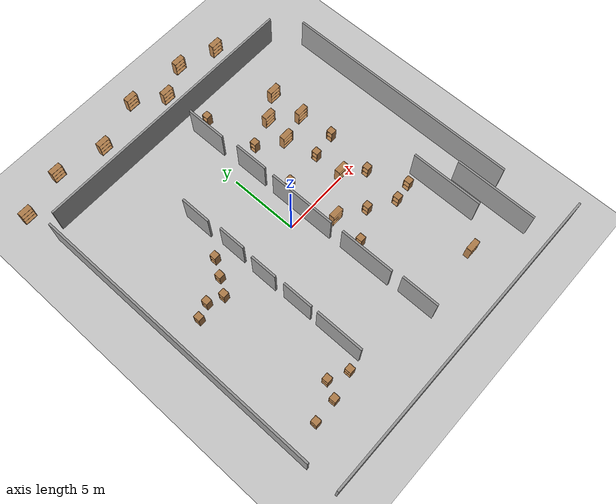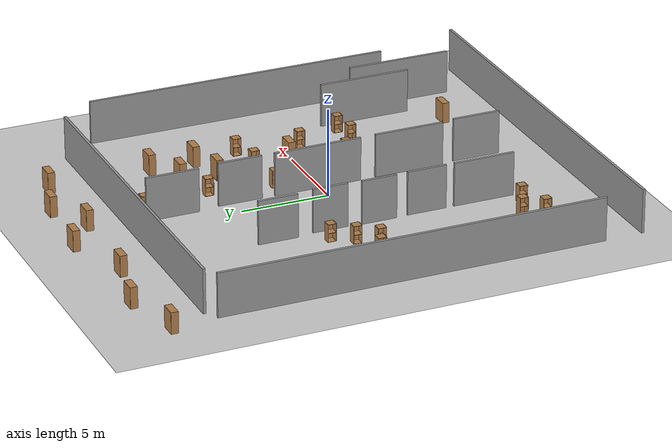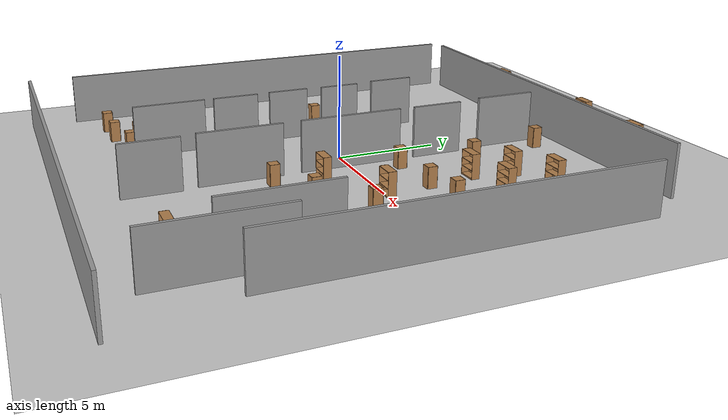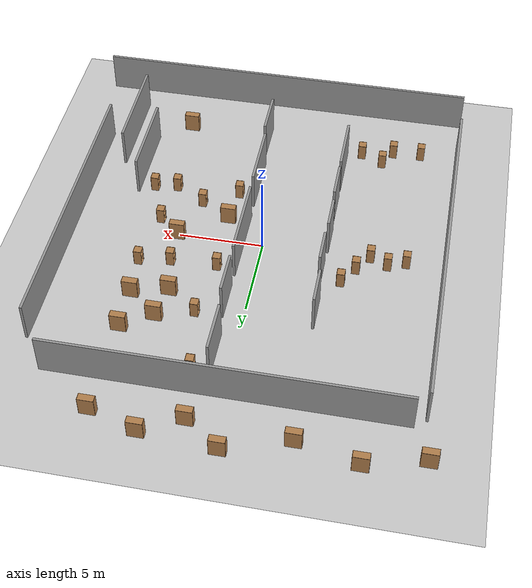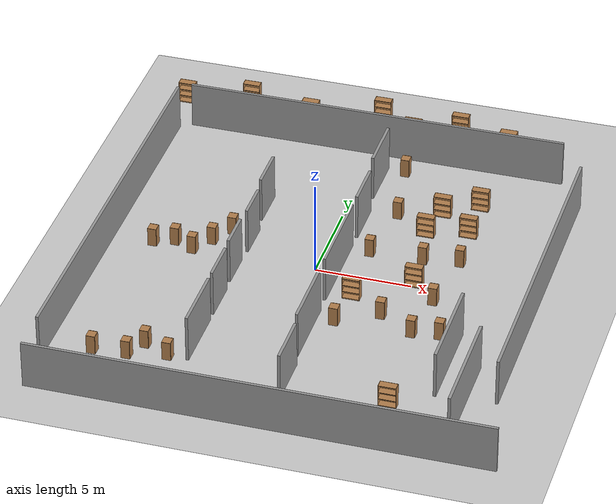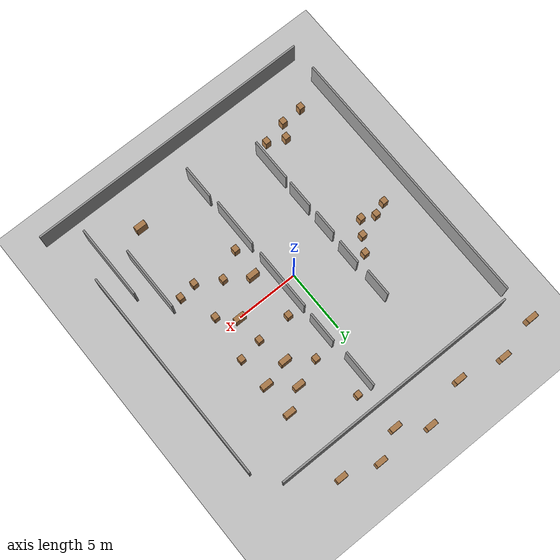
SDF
<sdf version="1.6">
 <world name="default">
  <light name="sun" type="directional">
   <pose>0 0 10 0 -0 0</pose>
   <diffuse>0.8 0.8 0.8 1</diffuse>
   <specular>0.2 0.2 0.2 1</specular>
   <attenuation>
    <range>1000</range>
    <constant>0.9</constant>
    <linear>0.01</linear>
    <quadratic>0.001</quadratic>
   </attenuation>
   <direction>-0.5 0.1 -0.9</direction>
  </light>
  <model name="ground_plane">
   <static>1</static>
   <link name="link">
    <collision name="collision">
     <geometry><plane><normal>0 0 1</normal><size>100 100</size></plane></geometry>
     <surface><friction><ode><mu>100</mu><mu2>50</mu2></ode></friction></surface>
    </collision>
    <visual name="visual">
     <cast_shadows>0</cast_shadows>
     <geometry><plane><normal>0 0 1</normal><size>100 100</size></plane></geometry>
     <material>
      <script><uri>file://media/materials/scripts/gazebo.material</uri><name>Gazebo/Grey</name></script>
     </material>
    </visual>
   </link>
  </model>
  <gravity>0 0 -9.8</gravity>
  <magnetic_field>6e-06 2.3e-05 -4.2e-05</magnetic_field>
  <atmosphere type="adiabatic"/>
  <physics name="default_physics" default="0" type="ode">
   <max_step_size>0.001</max_step_size>
   <real_time_factor>1</real_time_factor>
   <real_time_update_rate>1000</real_time_update_rate>
  </physics>
  <scene><ambient>0.4 0.4 0.4 1</ambient><background>0.7 0.7 0.7 1</background><shadows>1</shadows></scene>
  <audio><device>default</device></audio>
  <spherical_coordinates>
   <surface_model>EARTH_WGS84</surface_model>
   <latitude_deg>0</latitude_deg>
   <longitude_deg>0</longitude_deg>
   <elevation>0</elevation>
   <heading_deg>0</heading_deg>
  </spherical_coordinates>
  <model name="room13">
   <pose>0.954406 -1.0163 0 0 -0 0</pose>
   <link name="Wall_0">
    <collision name="Wall_0_Collision">
     <geometry><box><size>20.25 0.15 2.5</size></box></geometry>
     <pose>0 0 1.25 0 -0 0</pose>
    </collision>
    <visual name="Wall_0_Visual">
     <pose>0 0 1.25 0 -0 0</pose>
     <geometry><box><size>20.25 0.15 2.5</size></box></geometry>
     <material>
      <script><uri>file://media/materials/scripts/gazebo.material</uri><name>Gazebo/Grey</name></script>
      <ambient>1 1 1 1</ambient>
     </material>
     <meta><layer>0</layer></meta>
    </visual>
    <pose>-0.956756 12.1861 0 0 -0 0</pose>
   </link>
   <link name="Wall_10">
    <collision name="Wall_10_Collision">
     <geometry><box><size>2.75 0.15 2.5</size></box></geometry>
     <pose>0 0 1.25 0 -0 0</pose>
    </collision>
    <visual name="Wall_10_Visual">
     <pose>0 0 1.25 0 -0 0</pose>
     <geometry><box><size>2.75 0.15 2.5</size></box></geometry>
     <material>
      <script><uri>file://media/materials/scripts/gazebo.material</uri><name>Gazebo/Grey</name></script>
      <ambient>1 1 1 1</ambient>
     </material>
     <meta><layer>0</layer></meta>
    </visual>
    <pose>0.401491 -8.32568 0 0 -0 -1.5708</pose>
   </link>
   <link name="Wall_12">
    <collision name="Wall_12_Collision">
     <geometry><box><size>3 0.15 2.5</size></box></geometry>
     <pose>0 0 1.25 0 -0 0</pose>
    </collision>
    <visual name="Wall_12_Visual">
     <pose>0 0 1.25 0 -0 0</pose>
     <geometry><box><size>3 0.15 2.5</size></box></geometry>
     <material>
      <script><uri>file://media/materials/scripts/gazebo.material</uri><name>Gazebo/Grey</name></script>
      <ambient>1 1 1 1</ambient>
     </material>
     <meta><layer>0</layer></meta>
    </visual>
    <pose>0.055689 9.53105 0 0 -0 -1.5708</pose>
   </link>
   <link name="Wall_15">
    <collision name="Wall_15_Collision">
     <geometry><box><size>17.5 0.15 2.5</size></box></geometry>
     <pose>0 0 1.25 0 -0 0</pose>
    </collision>
    <visual name="Wall_15_Visual">
     <pose>0 0 1.25 0 -0 0</pose>
     <geometry><box><size>17.5 0.15 2.5</size></box></geometry>
     <material>
      <script><uri>file://media/materials/scripts/gazebo.material</uri><name>Gazebo/Grey</name></script>
      <ambient>1 1 1 1</ambient>
     </material>
     <meta><layer>0</layer></meta>
    </visual>
    <pose>10.5096 1.53625 0 0 -0 -1.5708</pose>
   </link>
   <link name="Wall_17">
    <collision name="Wall_17_Collision">
     <geometry><box><size>23.5 0.15 2.5</size></box></geometry>
     <pose>0 0 1.25 0 -0 0</pose>
    </collision>
    <visual name="Wall_17_Visual">
     <pose>0 0 1.25 0 -0 0</pose>
     <geometry><box><size>23.5 0.15 2.5</size></box></geometry>
     <material>
      <script><uri>file://media/materials/scripts/gazebo.material</uri><name>Gazebo/Grey</name></script>
      <ambient>1 1 1 1</ambient>
     </material>
     <meta><layer>0</layer></meta>
    </visual>
    <pose>0.026601 -12.1861 0 0 -0 0</pose>
   </link>
   <link name="Wall_19">
    <collision name="Wall_19_Collision">
     <geometry><box><size>6 0.15 2.5</size></box></geometry>
     <pose>0 0 1.25 0 -0 0</pose>
    </collision>
    <visual name="Wall_19_Visual">
     <pose>0 0 1.25 0 -0 0</pose>
     <geometry><box><size>6 0.15 2.5</size></box></geometry>
     <material>
      <script><uri>file://media/materials/scripts/gazebo.material</uri><name>Gazebo/Grey</name></script>
      <ambient>1 1 1 1</ambient>
     </material>
     <meta><layer>0</layer></meta>
    </visual>
    <pose>9.01995 -7.63647 0 0 -0 -1.5708</pose>
   </link>
   <link name="Wall_2">
    <collision name="Wall_2_Collision">
     <geometry><box><size>21.75 0.15 2.5</size></box></geometry>
     <pose>0 0 1.25 0 -0 0</pose>
    </collision>
    <visual name="Wall_2_Visual">
     <pose>0 0 1.25 0 -0 0</pose>
     <geometry><box><size>21.75 0.15 2.5</size></box></geometry>
     <material>
      <script><uri>file://media/materials/scripts/gazebo.material</uri><name>Gazebo/Grey</name></script>
      <ambient>1 1 1 1</ambient>
     </material>
     <meta><layer>0</layer></meta>
    </visual>
    <pose>-11.7016 0.874258 0 0 -0 -1.5708</pose>
   </link>
   <link name="Wall_21">
    <collision name="Wall_21_Collision">
     <geometry><box><size>5.25 0.15 2.5</size></box></geometry>
     <pose>0 0 1.25 0 -0 0</pose>
    </collision>
    <visual name="Wall_21_Visual">
     <pose>0 0 1.25 0 -0 0</pose>
     <geometry><box><size>5.25 0.15 2.5</size></box></geometry>
     <material>
      <script><uri>file://media/materials/scripts/gazebo.material</uri><name>Gazebo/Grey</name></script>
      <ambient>1 1 1 1</ambient>
     </material>
     <meta><layer>0</layer></meta>
    </visual>
    <pose>7.50375 -4.84809 0 0 -0 1.5708</pose>
   </link>
   <link name="Wall_23">
    <collision name="Wall_23_Collision">
     <geometry><box><size>3.5 0.15 2.5</size></box></geometry>
     <pose>0 0 1.25 0 -0 0</pose>
    </collision>
    <visual name="Wall_23_Visual">
     <pose>0 0 1.25 0 -0 0</pose>
     <geometry><box><size>3.5 0.15 2.5</size></box></geometry>
     <material>
      <script><uri>file://media/materials/scripts/gazebo.material</uri><name>Gazebo/Grey</name></script>
      <ambient>1 1 1 1</ambient>
     </material>
     <meta><layer>0</layer></meta>
    </visual>
    <pose>-4.75895 -6.30829 0 0 -0 1.5708</pose>
   </link>
   <link name="Wall_25">
    <collision name="Wall_25_Collision">
     <geometry><box><size>2.25 0.15 2.5</size></box></geometry>
     <pose>0 0 1.25 0 -0 0</pose>
    </collision>
    <visual name="Wall_25_Visual">
     <pose>0 0 1.25 0 -0 0</pose>
     <geometry><box><size>2.25 0.15 2.5</size></box></geometry>
     <material>
      <script><uri>file://media/materials/scripts/gazebo.material</uri><name>Gazebo/Grey</name></script>
      <ambient>1 1 1 1</ambient>
     </material>
     <meta><layer>0</layer></meta>
    </visual>
    <pose>-4.75895 -2.96986 0 0 -0 1.5708</pose>
   </link>
   <link name="Wall_27">
    <collision name="Wall_27_Collision">
     <geometry><box><size>2 0.15 2.5</size></box></geometry>
     <pose>0 0 1.25 0 -0 0</pose>
    </collision>
    <visual name="Wall_27_Visual">
     <pose>0 0 1.25 0 -0 0</pose>
     <geometry><box><size>2 0.15 2.5</size></box></geometry>
     <material>
      <script><uri>file://media/materials/scripts/gazebo.material</uri><name>Gazebo/Grey</name></script>
      <ambient>1 1 1 1</ambient>
     </material>
     <meta><layer>0</layer></meta>
    </visual>
    <pose>-4.81215 -0.195438 0 0 -0 1.5708</pose>
   </link>
   <link name="Wall_29">
    <collision name="Wall_29_Collision">
     <geometry><box><size>2 0.15 2.5</size></box></geometry>
     <pose>0 0 1.25 0 -0 0</pose>
    </collision>
    <visual name="Wall_29_Visual">
     <pose>0 0 1.25 0 -0 0</pose>
     <geometry><box><size>2 0.15 2.5</size></box></geometry>
     <material>
      <script><uri>file://media/materials/scripts/gazebo.material</uri><name>Gazebo/Grey</name></script>
      <ambient>1 1 1 1</ambient>
     </material>
     <meta><layer>0</layer></meta>
    </visual>
    <pose>-4.73235 2.57098 0 0 -0 1.5708</pose>
   </link>
   <link name="Wall_31">
    <collision name="Wall_31_Collision">
     <geometry><box><size>2.25 0.15 2.5</size></box></geometry>
     <pose>0 0 1.25 0 -0 0</pose>
    </collision>
    <visual name="Wall_31_Visual">
     <pose>0 0 1.25 0 -0 0</pose>
     <geometry><box><size>2.25 0.15 2.5</size></box></geometry>
     <material>
      <script><uri>file://media/materials/scripts/gazebo.material</uri><name>Gazebo/Grey</name></script>
      <ambient>1 1 1 1</ambient>
     </material>
     <meta><layer>0</layer></meta>
    </visual>
    <pose>-4.89195 5.59541 0 0 -0 1.5708</pose>
   </link>
   <link name="Wall_4">
    <collision name="Wall_4_Collision">
     <geometry><box><size>2.5 0.15 2.5</size></box></geometry>
     <pose>0 0 1.25 0 -0 0</pose>
    </collision>
    <visual name="Wall_4_Visual">
     <pose>0 0 1.25 0 -0 0</pose>
     <geometry><box><size>2.5 0.15 2.5</size></box></geometry>
     <material>
      <script><uri>file://media/materials/scripts/gazebo.material</uri><name>Gazebo/Grey</name></script>
      <ambient>1 1 1 1</ambient>
     </material>
     <meta><layer>0</layer></meta>
    </visual>
    <pose>0.24189 5.61584 0 0 -0 -1.5708</pose>
   </link>
   <link name="Wall_6">
    <collision name="Wall_6_Collision">
     <geometry><box><size>5 0.15 2.5</size></box></geometry>
     <pose>0 0 1.25 0 -0 0</pose>
    </collision>
    <visual name="Wall_6_Visual">
     <pose>0 0 1.25 0 -0 0</pose>
     <geometry><box><size>5 0.15 2.5</size></box></geometry>
     <material>
      <script><uri>file://media/materials/scripts/gazebo.material</uri><name>Gazebo/Grey</name></script>
      <ambient>1 1 1 1</ambient>
     </material>
     <meta><layer>0</layer></meta>
    </visual>
    <pose>0.21529 1.1362 0 0 -0 -1.5708</pose>
   </link>
   <link name="Wall_8">
    <collision name="Wall_8_Collision">
     <geometry><box><size>4 0.15 2.5</size></box></geometry>
     <pose>0 0 1.25 0 -0 0</pose>
    </collision>
    <visual name="Wall_8_Visual">
     <pose>0 0 1.25 0 -0 0</pose>
     <geometry><box><size>4 0.15 2.5</size></box></geometry>
     <material>
      <script><uri>file://media/materials/scripts/gazebo.material</uri><name>Gazebo/Grey</name></script>
      <ambient>1 1 1 1</ambient>
     </material>
     <meta><layer>0</layer></meta>
    </visual>
    <pose>0.24189 -4.24245 0 0 -0 -1.5708</pose>
   </link>
   <static>1</static>
  </model>
  <model name="bookshelf">
   <static>1</static>
   <link name="link">
    <inertial><mass>1</mass></inertial>
    <collision name="back">
     <pose>0 0.005 0.6 0 -0 0</pose>
     <geometry><box><size>0.9 0.01 1.2</size></box></geometry>
    </collision>
    <visual name="visual1">
     <pose>0 0.005 0.6 0 -0 0</pose>
     <geometry><box><size>0.9 0.01 1.2</size></box></geometry>
     <material>
      <script><uri>file://media/materials/scripts/gazebo.material</uri><name>Gazebo/Wood</name></script>
     </material>
    </visual>
    <collision name="left_side">
     <pose>0.45 -0.195 0.6 0 -0 0</pose>
     <geometry><box><size>0.02 0.4 1.2</size></box></geometry>
    </collision>
    <visual name="visual2">
     <pose>0.45 -0.195 0.6 0 -0 0</pose>
     <geometry><box><size>0.02 0.4 1.2</size></box></geometry>
     <material>
      <script><uri>file://media/materials/scripts/gazebo.material</uri><name>Gazebo/Wood</name></script>
     </material>
    </visual>
    <collision name="right_side">
     <pose>-0.45 -0.195 0.6 0 -0 0</pose>
     <geometry><box><size>0.02 0.4 1.2</size></box></geometry>
    </collision>
    <visual name="visual3">
     <pose>-0.45 -0.195 0.6 0 -0 0</pose>
     <geometry><box><size>0.02 0.4 1.2</size></box></geometry>
     <material>
      <script><uri>file://media/materials/scripts/gazebo.material</uri><name>Gazebo/Wood</name></script>
     </material>
    </visual>
    <collision name="bottom">
     <pose>0 -0.195 0.03 0 -0 0</pose>
     <geometry><box><size>0.88 0.4 0.06</size></box></geometry>
    </collision>
    <visual name="visual4">
     <pose>0 -0.195 0.03 0 -0 0</pose>
     <geometry><box><size>0.88 0.4 0.06</size></box></geometry>
     <material>
      <script><uri>file://media/materials/scripts/gazebo.material</uri><name>Gazebo/Wood</name></script>
     </material>
    </visual>
    <collision name="top">
     <pose>0 -0.195 1.19 0 -0 0</pose>
     <geometry><box><size>0.88 0.4 0.02</size></box></geometry>
    </collision>
    <visual name="visual5">
     <pose>0 -0.195 1.19 0 -0 0</pose>
     <geometry><box><size>0.88 0.4 0.02</size></box></geometry>
     <material>
      <script><uri>file://media/materials/scripts/gazebo.material</uri><name>Gazebo/Wood</name></script>
     </material>
    </visual>
    <collision name="low_shelf">
     <pose>0 -0.195 0.43 0 -0 0</pose>
     <geometry><box><size>0.88 0.4 0.02</size></box></geometry>
    </collision>
    <visual name="visual6">
     <pose>0 -0.195 0.43 0 -0 0</pose>
     <geometry><box><size>0.88 0.4 0.02</size></box></geometry>
     <material>
      <script><uri>file://media/materials/scripts/gazebo.material</uri><name>Gazebo/Wood</name></script>
     </material>
    </visual>
    <collision name="high_shelf">
     <pose>0 -0.195 0.8 0 -0 0</pose>
     <geometry><box><size>0.88 0.4 0.02</size></box></geometry>
    </collision>
    <visual name="visual7">
     <pose>0 -0.195 0.8 0 -0 0</pose>
     <geometry><box><size>0.88 0.4 0.02</size></box></geometry>
     <material>
      <script><uri>file://media/materials/scripts/gazebo.material</uri><name>Gazebo/Wood</name></script>
     </material>
    </visual>
   </link>
   <pose>-11.0786 13.5048 0 0 -0 0</pose>
  </model>
  <model name="bookshelf_0">
   <static>1</static>
   <link name="link">
    <inertial><mass>1</mass></inertial>
    <collision name="back">
     <pose>0 0.005 0.6 0 -0 0</pose>
     <geometry><box><size>0.9 0.01 1.2</size></box></geometry>
    </collision>
    <visual name="visual1">
     <pose>0 0.005 0.6 0 -0 0</pose>
     <geometry><box><size>0.9 0.01 1.2</size></box></geometry>
     <material>
      <script><uri>file://media/materials/scripts/gazebo.material</uri><name>Gazebo/Wood</name></script>
     </material>
    </visual>
    <collision name="left_side">
     <pose>0.45 -0.195 0.6 0 -0 0</pose>
     <geometry><box><size>0.02 0.4 1.2</size></box></geometry>
    </collision>
    <visual name="visual2">
     <pose>0.45 -0.195 0.6 0 -0 0</pose>
     <geometry><box><size>0.02 0.4 1.2</size></box></geometry>
     <material>
      <script><uri>file://media/materials/scripts/gazebo.material</uri><name>Gazebo/Wood</name></script>
     </material>
    </visual>
    <collision name="right_side">
     <pose>-0.45 -0.195 0.6 0 -0 0</pose>
     <geometry><box><size>0.02 0.4 1.2</size></box></geometry>
    </collision>
    <visual name="visual3">
     <pose>-0.45 -0.195 0.6 0 -0 0</pose>
     <geometry><box><size>0.02 0.4 1.2</size></box></geometry>
     <material>
      <script><uri>file://media/materials/scripts/gazebo.material</uri><name>Gazebo/Wood</name></script>
     </material>
    </visual>
    <collision name="bottom">
     <pose>0 -0.195 0.03 0 -0 0</pose>
     <geometry><box><size>0.88 0.4 0.06</size></box></geometry>
    </collision>
    <visual name="visual4">
     <pose>0 -0.195 0.03 0 -0 0</pose>
     <geometry><box><size>0.88 0.4 0.06</size></box></geometry>
     <material>
      <script><uri>file://media/materials/scripts/gazebo.material</uri><name>Gazebo/Wood</name></script>
     </material>
    </visual>
    <collision name="top">
     <pose>0 -0.195 1.19 0 -0 0</pose>
     <geometry><box><size>0.88 0.4 0.02</size></box></geometry>
    </collision>
    <visual name="visual5">
     <pose>0 -0.195 1.19 0 -0 0</pose>
     <geometry><box><size>0.88 0.4 0.02</size></box></geometry>
     <material>
      <script><uri>file://media/materials/scripts/gazebo.material</uri><name>Gazebo/Wood</name></script>
     </material>
    </visual>
    <collision name="low_shelf">
     <pose>0 -0.195 0.43 0 -0 0</pose>
     <geometry><box><size>0.88 0.4 0.02</size></box></geometry>
    </collision>
    <visual name="visual6">
     <pose>0 -0.195 0.43 0 -0 0</pose>
     <geometry><box><size>0.88 0.4 0.02</size></box></geometry>
     <material>
      <script><uri>file://media/materials/scripts/gazebo.material</uri><name>Gazebo/Wood</name></script>
     </material>
    </visual>
    <collision name="high_shelf">
     <pose>0 -0.195 0.8 0 -0 0</pose>
     <geometry><box><size>0.88 0.4 0.02</size></box></geometry>
    </collision>
    <visual name="visual7">
     <pose>0 -0.195 0.8 0 -0 0</pose>
     <geometry><box><size>0.88 0.4 0.02</size></box></geometry>
     <material>
      <script><uri>file://media/materials/scripts/gazebo.material</uri><name>Gazebo/Wood</name></script>
     </material>
    </visual>
   </link>
   <pose>-7.72125 14.3757 0 0 -0 0</pose>
  </model>
  <model name="bookshelf_1">
   <static>1</static>
   <link name="link">
    <inertial><mass>1</mass></inertial>
    <collision name="back">
     <pose>0 0.005 0.6 0 -0 0</pose>
     <geometry><box><size>0.9 0.01 1.2</size></box></geometry>
    </collision>
    <visual name="visual1">
     <pose>0 0.005 0.6 0 -0 0</pose>
     <geometry><box><size>0.9 0.01 1.2</size></box></geometry>
     <material>
      <script><uri>file://media/materials/scripts/gazebo.material</uri><name>Gazebo/Wood</name></script>
     </material>
    </visual>
    <collision name="left_side">
     <pose>0.45 -0.195 0.6 0 -0 0</pose>
     <geometry><box><size>0.02 0.4 1.2</size></box></geometry>
    </collision>
    <visual name="visual2">
     <pose>0.45 -0.195 0.6 0 -0 0</pose>
     <geometry><box><size>0.02 0.4 1.2</size></box></geometry>
     <material>
      <script><uri>file://media/materials/scripts/gazebo.material</uri><name>Gazebo/Wood</name></script>
     </material>
    </visual>
    <collision name="right_side">
     <pose>-0.45 -0.195 0.6 0 -0 0</pose>
     <geometry><box><size>0.02 0.4 1.2</size></box></geometry>
    </collision>
    <visual name="visual3">
     <pose>-0.45 -0.195 0.6 0 -0 0</pose>
     <geometry><box><size>0.02 0.4 1.2</size></box></geometry>
     <material>
      <script><uri>file://media/materials/scripts/gazebo.material</uri><name>Gazebo/Wood</name></script>
     </material>
    </visual>
    <collision name="bottom">
     <pose>0 -0.195 0.03 0 -0 0</pose>
     <geometry><box><size>0.88 0.4 0.06</size></box></geometry>
    </collision>
    <visual name="visual4">
     <pose>0 -0.195 0.03 0 -0 0</pose>
     <geometry><box><size>0.88 0.4 0.06</size></box></geometry>
     <material>
      <script><uri>file://media/materials/scripts/gazebo.material</uri><name>Gazebo/Wood</name></script>
     </material>
    </visual>
    <collision name="top">
     <pose>0 -0.195 1.19 0 -0 0</pose>
     <geometry><box><size>0.88 0.4 0.02</size></box></geometry>
    </collision>
    <visual name="visual5">
     <pose>0 -0.195 1.19 0 -0 0</pose>
     <geometry><box><size>0.88 0.4 0.02</size></box></geometry>
     <material>
      <script><uri>file://media/materials/scripts/gazebo.material</uri><name>Gazebo/Wood</name></script>
     </material>
    </visual>
    <collision name="low_shelf">
     <pose>0 -0.195 0.43 0 -0 0</pose>
     <geometry><box><size>0.88 0.4 0.02</size></box></geometry>
    </collision>
    <visual name="visual6">
     <pose>0 -0.195 0.43 0 -0 0</pose>
     <geometry><box><size>0.88 0.4 0.02</size></box></geometry>
     <material>
      <script><uri>file://media/materials/scripts/gazebo.material</uri><name>Gazebo/Wood</name></script>
     </material>
    </visual>
    <collision name="high_shelf">
     <pose>0 -0.195 0.8 0 -0 0</pose>
     <geometry><box><size>0.88 0.4 0.02</size></box></geometry>
    </collision>
    <visual name="visual7">
     <pose>0 -0.195 0.8 0 -0 0</pose>
     <geometry><box><size>0.88 0.4 0.02</size></box></geometry>
     <material>
      <script><uri>file://media/materials/scripts/gazebo.material</uri><name>Gazebo/Wood</name></script>
     </material>
    </visual>
   </link>
   <pose>-4.19439 13.5916 0 0 -0 0</pose>
  </model>
  <model name="bookshelf_2">
   <static>1</static>
   <link name="link">
    <inertial><mass>1</mass></inertial>
    <collision name="back">
     <pose>0 0.005 0.6 0 -0 0</pose>
     <geometry><box><size>0.9 0.01 1.2</size></box></geometry>
    </collision>
    <visual name="visual1">
     <pose>0 0.005 0.6 0 -0 0</pose>
     <geometry><box><size>0.9 0.01 1.2</size></box></geometry>
     <material>
      <script><uri>file://media/materials/scripts/gazebo.material</uri><name>Gazebo/Wood</name></script>
     </material>
    </visual>
    <collision name="left_side">
     <pose>0.45 -0.195 0.6 0 -0 0</pose>
     <geometry><box><size>0.02 0.4 1.2</size></box></geometry>
    </collision>
    <visual name="visual2">
     <pose>0.45 -0.195 0.6 0 -0 0</pose>
     <geometry><box><size>0.02 0.4 1.2</size></box></geometry>
     <material>
      <script><uri>file://media/materials/scripts/gazebo.material</uri><name>Gazebo/Wood</name></script>
     </material>
    </visual>
    <collision name="right_side">
     <pose>-0.45 -0.195 0.6 0 -0 0</pose>
     <geometry><box><size>0.02 0.4 1.2</size></box></geometry>
    </collision>
    <visual name="visual3">
     <pose>-0.45 -0.195 0.6 0 -0 0</pose>
     <geometry><box><size>0.02 0.4 1.2</size></box></geometry>
     <material>
      <script><uri>file://media/materials/scripts/gazebo.material</uri><name>Gazebo/Wood</name></script>
     </material>
    </visual>
    <collision name="bottom">
     <pose>0 -0.195 0.03 0 -0 0</pose>
     <geometry><box><size>0.88 0.4 0.06</size></box></geometry>
    </collision>
    <visual name="visual4">
     <pose>0 -0.195 0.03 0 -0 0</pose>
     <geometry><box><size>0.88 0.4 0.06</size></box></geometry>
     <material>
      <script><uri>file://media/materials/scripts/gazebo.material</uri><name>Gazebo/Wood</name></script>
     </material>
    </visual>
    <collision name="top">
     <pose>0 -0.195 1.19 0 -0 0</pose>
     <geometry><box><size>0.88 0.4 0.02</size></box></geometry>
    </collision>
    <visual name="visual5">
     <pose>0 -0.195 1.19 0 -0 0</pose>
     <geometry><box><size>0.88 0.4 0.02</size></box></geometry>
     <material>
      <script><uri>file://media/materials/scripts/gazebo.material</uri><name>Gazebo/Wood</name></script>
     </material>
    </visual>
    <collision name="low_shelf">
     <pose>0 -0.195 0.43 0 -0 0</pose>
     <geometry><box><size>0.88 0.4 0.02</size></box></geometry>
    </collision>
    <visual name="visual6">
     <pose>0 -0.195 0.43 0 -0 0</pose>
     <geometry><box><size>0.88 0.4 0.02</size></box></geometry>
     <material>
      <script><uri>file://media/materials/scripts/gazebo.material</uri><name>Gazebo/Wood</name></script>
     </material>
    </visual>
    <collision name="high_shelf">
     <pose>0 -0.195 0.8 0 -0 0</pose>
     <geometry><box><size>0.88 0.4 0.02</size></box></geometry>
    </collision>
    <visual name="visual7">
     <pose>0 -0.195 0.8 0 -0 0</pose>
     <geometry><box><size>0.88 0.4 0.02</size></box></geometry>
     <material>
      <script><uri>file://media/materials/scripts/gazebo.material</uri><name>Gazebo/Wood</name></script>
     </material>
    </visual>
   </link>
   <pose>-0.499283 14.7908 0 0 -0 0</pose>
  </model>
  <model name="bookshelf_3">
   <static>1</static>
   <link name="link">
    <inertial><mass>1</mass></inertial>
    <collision name="back">
     <pose>0 0.005 0.6 0 -0 0</pose>
     <geometry><box><size>0.9 0.01 1.2</size></box></geometry>
    </collision>
    <visual name="visual1">
     <pose>0 0.005 0.6 0 -0 0</pose>
     <geometry><box><size>0.9 0.01 1.2</size></box></geometry>
     <material>
      <script><uri>file://media/materials/scripts/gazebo.material</uri><name>Gazebo/Wood</name></script>
     </material>
    </visual>
    <collision name="left_side">
     <pose>0.45 -0.195 0.6 0 -0 0</pose>
     <geometry><box><size>0.02 0.4 1.2</size></box></geometry>
    </collision>
    <visual name="visual2">
     <pose>0.45 -0.195 0.6 0 -0 0</pose>
     <geometry><box><size>0.02 0.4 1.2</size></box></geometry>
     <material>
      <script><uri>file://media/materials/scripts/gazebo.material</uri><name>Gazebo/Wood</name></script>
     </material>
    </visual>
    <collision name="right_side">
     <pose>-0.45 -0.195 0.6 0 -0 0</pose>
     <geometry><box><size>0.02 0.4 1.2</size></box></geometry>
    </collision>
    <visual name="visual3">
     <pose>-0.45 -0.195 0.6 0 -0 0</pose>
     <geometry><box><size>0.02 0.4 1.2</size></box></geometry>
     <material>
      <script><uri>file://media/materials/scripts/gazebo.material</uri><name>Gazebo/Wood</name></script>
     </material>
    </visual>
    <collision name="bottom">
     <pose>0 -0.195 0.03 0 -0 0</pose>
     <geometry><box><size>0.88 0.4 0.06</size></box></geometry>
    </collision>
    <visual name="visual4">
     <pose>0 -0.195 0.03 0 -0 0</pose>
     <geometry><box><size>0.88 0.4 0.06</size></box></geometry>
     <material>
      <script><uri>file://media/materials/scripts/gazebo.material</uri><name>Gazebo/Wood</name></script>
     </material>
    </visual>
    <collision name="top">
     <pose>0 -0.195 1.19 0 -0 0</pose>
     <geometry><box><size>0.88 0.4 0.02</size></box></geometry>
    </collision>
    <visual name="visual5">
     <pose>0 -0.195 1.19 0 -0 0</pose>
     <geometry><box><size>0.88 0.4 0.02</size></box></geometry>
     <material>
      <script><uri>file://media/materials/scripts/gazebo.material</uri><name>Gazebo/Wood</name></script>
     </material>
    </visual>
    <collision name="low_shelf">
     <pose>0 -0.195 0.43 0 -0 0</pose>
     <geometry><box><size>0.88 0.4 0.02</size></box></geometry>
    </collision>
    <visual name="visual6">
     <pose>0 -0.195 0.43 0 -0 0</pose>
     <geometry><box><size>0.88 0.4 0.02</size></box></geometry>
     <material>
      <script><uri>file://media/materials/scripts/gazebo.material</uri><name>Gazebo/Wood</name></script>
     </material>
    </visual>
    <collision name="high_shelf">
     <pose>0 -0.195 0.8 0 -0 0</pose>
     <geometry><box><size>0.88 0.4 0.02</size></box></geometry>
    </collision>
    <visual name="visual7">
     <pose>0 -0.195 0.8 0 -0 0</pose>
     <geometry><box><size>0.88 0.4 0.02</size></box></geometry>
     <material>
      <script><uri>file://media/materials/scripts/gazebo.material</uri><name>Gazebo/Wood</name></script>
     </material>
    </visual>
   </link>
   <pose>1.52908 13.309 0 0 -0 0</pose>
  </model>
  <model name="bookshelf_4">
   <static>1</static>
   <link name="link">
    <inertial><mass>1</mass></inertial>
    <collision name="back">
     <pose>0 0.005 0.6 0 -0 0</pose>
     <geometry><box><size>0.9 0.01 1.2</size></box></geometry>
    </collision>
    <visual name="visual1">
     <pose>0 0.005 0.6 0 -0 0</pose>
     <geometry><box><size>0.9 0.01 1.2</size></box></geometry>
     <material>
      <script><uri>file://media/materials/scripts/gazebo.material</uri><name>Gazebo/Wood</name></script>
     </material>
    </visual>
    <collision name="left_side">
     <pose>0.45 -0.195 0.6 0 -0 0</pose>
     <geometry><box><size>0.02 0.4 1.2</size></box></geometry>
    </collision>
    <visual name="visual2">
     <pose>0.45 -0.195 0.6 0 -0 0</pose>
     <geometry><box><size>0.02 0.4 1.2</size></box></geometry>
     <material>
      <script><uri>file://media/materials/scripts/gazebo.material</uri><name>Gazebo/Wood</name></script>
     </material>
    </visual>
    <collision name="right_side">
     <pose>-0.45 -0.195 0.6 0 -0 0</pose>
     <geometry><box><size>0.02 0.4 1.2</size></box></geometry>
    </collision>
    <visual name="visual3">
     <pose>-0.45 -0.195 0.6 0 -0 0</pose>
     <geometry><box><size>0.02 0.4 1.2</size></box></geometry>
     <material>
      <script><uri>file://media/materials/scripts/gazebo.material</uri><name>Gazebo/Wood</name></script>
     </material>
    </visual>
    <collision name="bottom">
     <pose>0 -0.195 0.03 0 -0 0</pose>
     <geometry><box><size>0.88 0.4 0.06</size></box></geometry>
    </collision>
    <visual name="visual4">
     <pose>0 -0.195 0.03 0 -0 0</pose>
     <geometry><box><size>0.88 0.4 0.06</size></box></geometry>
     <material>
      <script><uri>file://media/materials/scripts/gazebo.material</uri><name>Gazebo/Wood</name></script>
     </material>
    </visual>
    <collision name="top">
     <pose>0 -0.195 1.19 0 -0 0</pose>
     <geometry><box><size>0.88 0.4 0.02</size></box></geometry>
    </collision>
    <visual name="visual5">
     <pose>0 -0.195 1.19 0 -0 0</pose>
     <geometry><box><size>0.88 0.4 0.02</size></box></geometry>
     <material>
      <script><uri>file://media/materials/scripts/gazebo.material</uri><name>Gazebo/Wood</name></script>
     </material>
    </visual>
    <collision name="low_shelf">
     <pose>0 -0.195 0.43 0 -0 0</pose>
     <geometry><box><size>0.88 0.4 0.02</size></box></geometry>
    </collision>
    <visual name="visual6">
     <pose>0 -0.195 0.43 0 -0 0</pose>
     <geometry><box><size>0.88 0.4 0.02</size></box></geometry>
     <material>
      <script><uri>file://media/materials/scripts/gazebo.material</uri><name>Gazebo/Wood</name></script>
     </material>
    </visual>
    <collision name="high_shelf">
     <pose>0 -0.195 0.8 0 -0 0</pose>
     <geometry><box><size>0.88 0.4 0.02</size></box></geometry>
    </collision>
    <visual name="visual7">
     <pose>0 -0.195 0.8 0 -0 0</pose>
     <geometry><box><size>0.88 0.4 0.02</size></box></geometry>
     <material>
      <script><uri>file://media/materials/scripts/gazebo.material</uri><name>Gazebo/Wood</name></script>
     </material>
    </visual>
   </link>
   <pose>3.85039 14.4909 0 0 -0 0</pose>
  </model>
  <model name="bookshelf_5">
   <static>1</static>
   <link name="link">
    <inertial><mass>1</mass></inertial>
    <collision name="back">
     <pose>0 0.005 0.6 0 -0 0</pose>
     <geometry><box><size>0.9 0.01 1.2</size></box></geometry>
    </collision>
    <visual name="visual1">
     <pose>0 0.005 0.6 0 -0 0</pose>
     <geometry><box><size>0.9 0.01 1.2</size></box></geometry>
     <material>
      <script><uri>file://media/materials/scripts/gazebo.material</uri><name>Gazebo/Wood</name></script>
     </material>
    </visual>
    <collision name="left_side">
     <pose>0.45 -0.195 0.6 0 -0 0</pose>
     <geometry><box><size>0.02 0.4 1.2</size></box></geometry>
    </collision>
    <visual name="visual2">
     <pose>0.45 -0.195 0.6 0 -0 0</pose>
     <geometry><box><size>0.02 0.4 1.2</size></box></geometry>
     <material>
      <script><uri>file://media/materials/scripts/gazebo.material</uri><name>Gazebo/Wood</name></script>
     </material>
    </visual>
    <collision name="right_side">
     <pose>-0.45 -0.195 0.6 0 -0 0</pose>
     <geometry><box><size>0.02 0.4 1.2</size></box></geometry>
    </collision>
    <visual name="visual3">
     <pose>-0.45 -0.195 0.6 0 -0 0</pose>
     <geometry><box><size>0.02 0.4 1.2</size></box></geometry>
     <material>
      <script><uri>file://media/materials/scripts/gazebo.material</uri><name>Gazebo/Wood</name></script>
     </material>
    </visual>
    <collision name="bottom">
     <pose>0 -0.195 0.03 0 -0 0</pose>
     <geometry><box><size>0.88 0.4 0.06</size></box></geometry>
    </collision>
    <visual name="visual4">
     <pose>0 -0.195 0.03 0 -0 0</pose>
     <geometry><box><size>0.88 0.4 0.06</size></box></geometry>
     <material>
      <script><uri>file://media/materials/scripts/gazebo.material</uri><name>Gazebo/Wood</name></script>
     </material>
    </visual>
    <collision name="top">
     <pose>0 -0.195 1.19 0 -0 0</pose>
     <geometry><box><size>0.88 0.4 0.02</size></box></geometry>
    </collision>
    <visual name="visual5">
     <pose>0 -0.195 1.19 0 -0 0</pose>
     <geometry><box><size>0.88 0.4 0.02</size></box></geometry>
     <material>
      <script><uri>file://media/materials/scripts/gazebo.material</uri><name>Gazebo/Wood</name></script>
     </material>
    </visual>
    <collision name="low_shelf">
     <pose>0 -0.195 0.43 0 -0 0</pose>
     <geometry><box><size>0.88 0.4 0.02</size></box></geometry>
    </collision>
    <visual name="visual6">
     <pose>0 -0.195 0.43 0 -0 0</pose>
     <geometry><box><size>0.88 0.4 0.02</size></box></geometry>
     <material>
      <script><uri>file://media/materials/scripts/gazebo.material</uri><name>Gazebo/Wood</name></script>
     </material>
    </visual>
    <collision name="high_shelf">
     <pose>0 -0.195 0.8 0 -0 0</pose>
     <geometry><box><size>0.88 0.4 0.02</size></box></geometry>
    </collision>
    <visual name="visual7">
     <pose>0 -0.195 0.8 0 -0 0</pose>
     <geometry><box><size>0.88 0.4 0.02</size></box></geometry>
     <material>
      <script><uri>file://media/materials/scripts/gazebo.material</uri><name>Gazebo/Wood</name></script>
     </material>
    </visual>
   </link>
   <pose>6.68529 13.5954 0 0 -0 0</pose>
  </model>
  <model name="bookshelf_6">
   <static>1</static>
   <link name="link">
    <inertial><mass>1</mass></inertial>
    <collision name="back">
     <pose>0 0.005 0.6 0 -0 0</pose>
     <geometry><box><size>0.9 0.01 1.2</size></box></geometry>
    </collision>
    <visual name="visual1">
     <pose>0 0.005 0.6 0 -0 0</pose>
     <geometry><box><size>0.9 0.01 1.2</size></box></geometry>
     <material>
      <script><uri>file://media/materials/scripts/gazebo.material</uri><name>Gazebo/Wood</name></script>
     </material>
    </visual>
    <collision name="left_side">
     <pose>0.45 -0.195 0.6 0 -0 0</pose>
     <geometry><box><size>0.02 0.4 1.2</size></box></geometry>
    </collision>
    <visual name="visual2">
     <pose>0.45 -0.195 0.6 0 -0 0</pose>
     <geometry><box><size>0.02 0.4 1.2</size></box></geometry>
     <material>
      <script><uri>file://media/materials/scripts/gazebo.material</uri><name>Gazebo/Wood</name></script>
     </material>
    </visual>
    <collision name="right_side">
     <pose>-0.45 -0.195 0.6 0 -0 0</pose>
     <geometry><box><size>0.02 0.4 1.2</size></box></geometry>
    </collision>
    <visual name="visual3">
     <pose>-0.45 -0.195 0.6 0 -0 0</pose>
     <geometry><box><size>0.02 0.4 1.2</size></box></geometry>
     <material>
      <script><uri>file://media/materials/scripts/gazebo.material</uri><name>Gazebo/Wood</name></script>
     </material>
    </visual>
    <collision name="bottom">
     <pose>0 -0.195 0.03 0 -0 0</pose>
     <geometry><box><size>0.88 0.4 0.06</size></box></geometry>
    </collision>
    <visual name="visual4">
     <pose>0 -0.195 0.03 0 -0 0</pose>
     <geometry><box><size>0.88 0.4 0.06</size></box></geometry>
     <material>
      <script><uri>file://media/materials/scripts/gazebo.material</uri><name>Gazebo/Wood</name></script>
     </material>
    </visual>
    <collision name="top">
     <pose>0 -0.195 1.19 0 -0 0</pose>
     <geometry><box><size>0.88 0.4 0.02</size></box></geometry>
    </collision>
    <visual name="visual5">
     <pose>0 -0.195 1.19 0 -0 0</pose>
     <geometry><box><size>0.88 0.4 0.02</size></box></geometry>
     <material>
      <script><uri>file://media/materials/scripts/gazebo.material</uri><name>Gazebo/Wood</name></script>
     </material>
    </visual>
    <collision name="low_shelf">
     <pose>0 -0.195 0.43 0 -0 0</pose>
     <geometry><box><size>0.88 0.4 0.02</size></box></geometry>
    </collision>
    <visual name="visual6">
     <pose>0 -0.195 0.43 0 -0 0</pose>
     <geometry><box><size>0.88 0.4 0.02</size></box></geometry>
     <material>
      <script><uri>file://media/materials/scripts/gazebo.material</uri><name>Gazebo/Wood</name></script>
     </material>
    </visual>
    <collision name="high_shelf">
     <pose>0 -0.195 0.8 0 -0 0</pose>
     <geometry><box><size>0.88 0.4 0.02</size></box></geometry>
    </collision>
    <visual name="visual7">
     <pose>0 -0.195 0.8 0 -0 0</pose>
     <geometry><box><size>0.88 0.4 0.02</size></box></geometry>
     <material>
      <script><uri>file://media/materials/scripts/gazebo.material</uri><name>Gazebo/Wood</name></script>
     </material>
    </visual>
   </link>
   <pose>6.63156 7.85194 0 0 -0 0</pose>
  </model>
  <model name="bookshelf_7">
   <static>1</static>
   <link name="link">
    <inertial><mass>1</mass></inertial>
    <collision name="back">
     <pose>0 0.005 0.6 0 -0 0</pose>
     <geometry><box><size>0.9 0.01 1.2</size></box></geometry>
    </collision>
    <visual name="visual1">
     <pose>0 0.005 0.6 0 -0 0</pose>
     <geometry><box><size>0.9 0.01 1.2</size></box></geometry>
     <material>
      <script><uri>file://media/materials/scripts/gazebo.material</uri><name>Gazebo/Wood</name></script>
     </material>
    </visual>
    <collision name="left_side">
     <pose>0.45 -0.195 0.6 0 -0 0</pose>
     <geometry><box><size>0.02 0.4 1.2</size></box></geometry>
    </collision>
    <visual name="visual2">
     <pose>0.45 -0.195 0.6 0 -0 0</pose>
     <geometry><box><size>0.02 0.4 1.2</size></box></geometry>
     <material>
      <script><uri>file://media/materials/scripts/gazebo.material</uri><name>Gazebo/Wood</name></script>
     </material>
    </visual>
    <collision name="right_side">
     <pose>-0.45 -0.195 0.6 0 -0 0</pose>
     <geometry><box><size>0.02 0.4 1.2</size></box></geometry>
    </collision>
    <visual name="visual3">
     <pose>-0.45 -0.195 0.6 0 -0 0</pose>
     <geometry><box><size>0.02 0.4 1.2</size></box></geometry>
     <material>
      <script><uri>file://media/materials/scripts/gazebo.material</uri><name>Gazebo/Wood</name></script>
     </material>
    </visual>
    <collision name="bottom">
     <pose>0 -0.195 0.03 0 -0 0</pose>
     <geometry><box><size>0.88 0.4 0.06</size></box></geometry>
    </collision>
    <visual name="visual4">
     <pose>0 -0.195 0.03 0 -0 0</pose>
     <geometry><box><size>0.88 0.4 0.06</size></box></geometry>
     <material>
      <script><uri>file://media/materials/scripts/gazebo.material</uri><name>Gazebo/Wood</name></script>
     </material>
    </visual>
    <collision name="top">
     <pose>0 -0.195 1.19 0 -0 0</pose>
     <geometry><box><size>0.88 0.4 0.02</size></box></geometry>
    </collision>
    <visual name="visual5">
     <pose>0 -0.195 1.19 0 -0 0</pose>
     <geometry><box><size>0.88 0.4 0.02</size></box></geometry>
     <material>
      <script><uri>file://media/materials/scripts/gazebo.material</uri><name>Gazebo/Wood</name></script>
     </material>
    </visual>
    <collision name="low_shelf">
     <pose>0 -0.195 0.43 0 -0 0</pose>
     <geometry><box><size>0.88 0.4 0.02</size></box></geometry>
    </collision>
    <visual name="visual6">
     <pose>0 -0.195 0.43 0 -0 0</pose>
     <geometry><box><size>0.88 0.4 0.02</size></box></geometry>
     <material>
      <script><uri>file://media/materials/scripts/gazebo.material</uri><name>Gazebo/Wood</name></script>
     </material>
    </visual>
    <collision name="high_shelf">
     <pose>0 -0.195 0.8 0 -0 0</pose>
     <geometry><box><size>0.88 0.4 0.02</size></box></geometry>
    </collision>
    <visual name="visual7">
     <pose>0 -0.195 0.8 0 -0 0</pose>
     <geometry><box><size>0.88 0.4 0.02</size></box></geometry>
     <material>
      <script><uri>file://media/materials/scripts/gazebo.material</uri><name>Gazebo/Wood</name></script>
     </material>
    </visual>
   </link>
   <pose>4.90371 6.74555 0 0 -0 0</pose>
  </model>
  <model name="bookshelf_8">
   <static>1</static>
   <link name="link">
    <inertial><mass>1</mass></inertial>
    <collision name="back">
     <pose>0 0.005 0.6 0 -0 0</pose>
     <geometry><box><size>0.9 0.01 1.2</size></box></geometry>
    </collision>
    <visual name="visual1">
     <pose>0 0.005 0.6 0 -0 0</pose>
     <geometry><box><size>0.9 0.01 1.2</size></box></geometry>
     <material>
      <script><uri>file://media/materials/scripts/gazebo.material</uri><name>Gazebo/Wood</name></script>
     </material>
    </visual>
    <collision name="left_side">
     <pose>0.45 -0.195 0.6 0 -0 0</pose>
     <geometry><box><size>0.02 0.4 1.2</size></box></geometry>
    </collision>
    <visual name="visual2">
     <pose>0.45 -0.195 0.6 0 -0 0</pose>
     <geometry><box><size>0.02 0.4 1.2</size></box></geometry>
     <material>
      <script><uri>file://media/materials/scripts/gazebo.material</uri><name>Gazebo/Wood</name></script>
     </material>
    </visual>
    <collision name="right_side">
     <pose>-0.45 -0.195 0.6 0 -0 0</pose>
     <geometry><box><size>0.02 0.4 1.2</size></box></geometry>
    </collision>
    <visual name="visual3">
     <pose>-0.45 -0.195 0.6 0 -0 0</pose>
     <geometry><box><size>0.02 0.4 1.2</size></box></geometry>
     <material>
      <script><uri>file://media/materials/scripts/gazebo.material</uri><name>Gazebo/Wood</name></script>
     </material>
    </visual>
    <collision name="bottom">
     <pose>0 -0.195 0.03 0 -0 0</pose>
     <geometry><box><size>0.88 0.4 0.06</size></box></geometry>
    </collision>
    <visual name="visual4">
     <pose>0 -0.195 0.03 0 -0 0</pose>
     <geometry><box><size>0.88 0.4 0.06</size></box></geometry>
     <material>
      <script><uri>file://media/materials/scripts/gazebo.material</uri><name>Gazebo/Wood</name></script>
     </material>
    </visual>
    <collision name="top">
     <pose>0 -0.195 1.19 0 -0 0</pose>
     <geometry><box><size>0.88 0.4 0.02</size></box></geometry>
    </collision>
    <visual name="visual5">
     <pose>0 -0.195 1.19 0 -0 0</pose>
     <geometry><box><size>0.88 0.4 0.02</size></box></geometry>
     <material>
      <script><uri>file://media/materials/scripts/gazebo.material</uri><name>Gazebo/Wood</name></script>
     </material>
    </visual>
    <collision name="low_shelf">
     <pose>0 -0.195 0.43 0 -0 0</pose>
     <geometry><box><size>0.88 0.4 0.02</size></box></geometry>
    </collision>
    <visual name="visual6">
     <pose>0 -0.195 0.43 0 -0 0</pose>
     <geometry><box><size>0.88 0.4 0.02</size></box></geometry>
     <material>
      <script><uri>file://media/materials/scripts/gazebo.material</uri><name>Gazebo/Wood</name></script>
     </material>
    </visual>
    <collision name="high_shelf">
     <pose>0 -0.195 0.8 0 -0 0</pose>
     <geometry><box><size>0.88 0.4 0.02</size></box></geometry>
    </collision>
    <visual name="visual7">
     <pose>0 -0.195 0.8 0 -0 0</pose>
     <geometry><box><size>0.88 0.4 0.02</size></box></geometry>
     <material>
      <script><uri>file://media/materials/scripts/gazebo.material</uri><name>Gazebo/Wood</name></script>
     </material>
    </visual>
   </link>
   <pose>6.652 5.28748 0 0 -0 0</pose>
  </model>
  <model name="bookshelf_9">
   <static>1</static>
   <link name="link">
    <inertial><mass>1</mass></inertial>
    <collision name="back">
     <pose>0 0.005 0.6 0 -0 0</pose>
     <geometry><box><size>0.9 0.01 1.2</size></box></geometry>
    </collision>
    <visual name="visual1">
     <pose>0 0.005 0.6 0 -0 0</pose>
     <geometry><box><size>0.9 0.01 1.2</size></box></geometry>
     <material>
      <script><uri>file://media/materials/scripts/gazebo.material</uri><name>Gazebo/Wood</name></script>
     </material>
    </visual>
    <collision name="left_side">
     <pose>0.45 -0.195 0.6 0 -0 0</pose>
     <geometry><box><size>0.02 0.4 1.2</size></box></geometry>
    </collision>
    <visual name="visual2">
     <pose>0.45 -0.195 0.6 0 -0 0</pose>
     <geometry><box><size>0.02 0.4 1.2</size></box></geometry>
     <material>
      <script><uri>file://media/materials/scripts/gazebo.material</uri><name>Gazebo/Wood</name></script>
     </material>
    </visual>
    <collision name="right_side">
     <pose>-0.45 -0.195 0.6 0 -0 0</pose>
     <geometry><box><size>0.02 0.4 1.2</size></box></geometry>
    </collision>
    <visual name="visual3">
     <pose>-0.45 -0.195 0.6 0 -0 0</pose>
     <geometry><box><size>0.02 0.4 1.2</size></box></geometry>
     <material>
      <script><uri>file://media/materials/scripts/gazebo.material</uri><name>Gazebo/Wood</name></script>
     </material>
    </visual>
    <collision name="bottom">
     <pose>0 -0.195 0.03 0 -0 0</pose>
     <geometry><box><size>0.88 0.4 0.06</size></box></geometry>
    </collision>
    <visual name="visual4">
     <pose>0 -0.195 0.03 0 -0 0</pose>
     <geometry><box><size>0.88 0.4 0.06</size></box></geometry>
     <material>
      <script><uri>file://media/materials/scripts/gazebo.material</uri><name>Gazebo/Wood</name></script>
     </material>
    </visual>
    <collision name="top">
     <pose>0 -0.195 1.19 0 -0 0</pose>
     <geometry><box><size>0.88 0.4 0.02</size></box></geometry>
    </collision>
    <visual name="visual5">
     <pose>0 -0.195 1.19 0 -0 0</pose>
     <geometry><box><size>0.88 0.4 0.02</size></box></geometry>
     <material>
      <script><uri>file://media/materials/scripts/gazebo.material</uri><name>Gazebo/Wood</name></script>
     </material>
    </visual>
    <collision name="low_shelf">
     <pose>0 -0.195 0.43 0 -0 0</pose>
     <geometry><box><size>0.88 0.4 0.02</size></box></geometry>
    </collision>
    <visual name="visual6">
     <pose>0 -0.195 0.43 0 -0 0</pose>
     <geometry><box><size>0.88 0.4 0.02</size></box></geometry>
     <material>
      <script><uri>file://media/materials/scripts/gazebo.material</uri><name>Gazebo/Wood</name></script>
     </material>
    </visual>
    <collision name="high_shelf">
     <pose>0 -0.195 0.8 0 -0 0</pose>
     <geometry><box><size>0.88 0.4 0.02</size></box></geometry>
    </collision>
    <visual name="visual7">
     <pose>0 -0.195 0.8 0 -0 0</pose>
     <geometry><box><size>0.88 0.4 0.02</size></box></geometry>
     <material>
      <script><uri>file://media/materials/scripts/gazebo.material</uri><name>Gazebo/Wood</name></script>
     </material>
    </visual>
   </link>
   <pose>4.53912 4.75708 0 0 -0 0</pose>
  </model>
  <model name="cabinet">
   <static>1</static>
   <link name="cabinet_bottom_plate">
    <inertial>
     <pose>0 0 -1 0 -0 0</pose>
     <inertia><ixx>2.05</ixx><ixy>0</ixy><ixz>0</ixz><iyy>2.05</iyy><iyz>0</iyz><izz>2.05</izz></inertia>
     <mass>25</mass>
    </inertial>
    <collision name="cabinet_bottom_plate_geom">
     <pose>0 0 0.01 0 -0 0</pose>
     <geometry><box><size>0.45 0.45 0.02</size></box></geometry>
    </collision>
    <visual name="cabinet_bottom_plate_geom_visual">
     <pose>0 0 0.01 0 -0 0</pose>
     <geometry><box><size>0.45 0.45 0.02</size></box></geometry>
     <material>
      <script><uri>file://media/materials/scripts/gazebo.material</uri><name>Gazebo/Wood</name></script>
     </material>
    </visual>
    <collision name="cabinet_bottom_plate_geom_cabinet_back_plate">
     <pose>0.235 0 0.51 0 -0 0</pose>
     <geometry><box><size>0.02 0.45 1.02</size></box></geometry>
    </collision>
    <visual name="cabinet_bottom_plate_geom_cabinet_back_plate_visual">
     <pose>0.235 0 0.51 0 -0 0</pose>
     <geometry><box><size>0.02 0.45 1.02</size></box></geometry>
     <material>
      <script><uri>file://media/materials/scripts/gazebo.material</uri><name>Gazebo/Wood</name></script>
     </material>
    </visual>
    <collision name="cabinet_bottom_plate_geom_cabinet_left_plate">
     <pose>0 0.235 0.51 0 -0 0</pose>
     <geometry><box><size>0.45 0.02 1.02</size></box></geometry>
    </collision>
    <visual name="cabinet_bottom_plate_geom_cabinet_left_plate_visual">
     <pose>0 0.235 0.51 0 -0 0</pose>
     <geometry><box><size>0.45 0.02 1.02</size></box></geometry>
     <material>
      <script><uri>file://media/materials/scripts/gazebo.material</uri><name>Gazebo/Wood</name></script>
     </material>
    </visual>
    <collision name="cabinet_bottom_plate_geom_cabinet_middle_plate">
     <pose>0 0 0.51 0 -0 0</pose>
     <geometry><box><size>0.45 0.45 0.02</size></box></geometry>
    </collision>
    <visual name="cabinet_bottom_plate_geom_cabinet_middle_plate_visual">
     <pose>0 0 0.51 0 -0 0</pose>
     <geometry><box><size>0.45 0.45 0.02</size></box></geometry>
     <material>
      <script><uri>file://media/materials/scripts/gazebo.material</uri><name>Gazebo/Wood</name></script>
     </material>
    </visual>
    <collision name="cabinet_bottom_plate_geom_cabinet_right_plate">
     <pose>0 -0.235 0.51 0 -0 0</pose>
     <geometry><box><size>0.45 0.02 1.02</size></box></geometry>
    </collision>
    <visual name="cabinet_bottom_plate_geom_cabinet_right_plate_visual">
     <pose>0 -0.235 0.51 0 -0 0</pose>
     <geometry><box><size>0.45 0.02 1.02</size></box></geometry>
     <material>
      <script><uri>file://media/materials/scripts/gazebo.material</uri><name>Gazebo/Wood</name></script>
     </material>
    </visual>
    <collision name="cabinet_bottom_plate_geom_cabinet_top_plate">
     <pose>0 0 1.01 0 -0 0</pose>
     <geometry><box><size>0.45 0.45 0.02</size></box></geometry>
    </collision>
    <visual name="cabinet_bottom_plate_geom_cabinet_top_plate_visual">
     <pose>0 0 1.01 0 -0 0</pose>
     <geometry><box><size>0.45 0.45 0.02</size></box></geometry>
     <material>
      <script><uri>file://media/materials/scripts/gazebo.material</uri><name>Gazebo/Wood</name></script>
     </material>
    </visual>
   </link>
   <pose>6.87325 2.52743 0 0 -0 0</pose>
  </model>
  <model name="cabinet_0">
   <static>1</static>
   <link name="cabinet_bottom_plate">
    <inertial>
     <pose>0 0 -1 0 -0 0</pose>
     <inertia><ixx>2.05</ixx><ixy>0</ixy><ixz>0</ixz><iyy>2.05</iyy><iyz>0</iyz><izz>2.05</izz></inertia>
     <mass>25</mass>
    </inertial>
    <collision name="cabinet_bottom_plate_geom">
     <pose>0 0 0.01 0 -0 0</pose>
     <geometry><box><size>0.45 0.45 0.02</size></box></geometry>
    </collision>
    <visual name="cabinet_bottom_plate_geom_visual">
     <pose>0 0 0.01 0 -0 0</pose>
     <geometry><box><size>0.45 0.45 0.02</size></box></geometry>
     <material>
      <script><uri>file://media/materials/scripts/gazebo.material</uri><name>Gazebo/Wood</name></script>
     </material>
    </visual>
    <collision name="cabinet_bottom_plate_geom_cabinet_back_plate">
     <pose>0.235 0 0.51 0 -0 0</pose>
     <geometry><box><size>0.02 0.45 1.02</size></box></geometry>
    </collision>
    <visual name="cabinet_bottom_plate_geom_cabinet_back_plate_visual">
     <pose>0.235 0 0.51 0 -0 0</pose>
     <geometry><box><size>0.02 0.45 1.02</size></box></geometry>
     <material>
      <script><uri>file://media/materials/scripts/gazebo.material</uri><name>Gazebo/Wood</name></script>
     </material>
    </visual>
    <collision name="cabinet_bottom_plate_geom_cabinet_left_plate">
     <pose>0 0.235 0.51 0 -0 0</pose>
     <geometry><box><size>0.45 0.02 1.02</size></box></geometry>
    </collision>
    <visual name="cabinet_bottom_plate_geom_cabinet_left_plate_visual">
     <pose>0 0.235 0.51 0 -0 0</pose>
     <geometry><box><size>0.45 0.02 1.02</size></box></geometry>
     <material>
      <script><uri>file://media/materials/scripts/gazebo.material</uri><name>Gazebo/Wood</name></script>
     </material>
    </visual>
    <collision name="cabinet_bottom_plate_geom_cabinet_middle_plate">
     <pose>0 0 0.51 0 -0 0</pose>
     <geometry><box><size>0.45 0.45 0.02</size></box></geometry>
    </collision>
    <visual name="cabinet_bottom_plate_geom_cabinet_middle_plate_visual">
     <pose>0 0 0.51 0 -0 0</pose>
     <geometry><box><size>0.45 0.45 0.02</size></box></geometry>
     <material>
      <script><uri>file://media/materials/scripts/gazebo.material</uri><name>Gazebo/Wood</name></script>
     </material>
    </visual>
    <collision name="cabinet_bottom_plate_geom_cabinet_right_plate">
     <pose>0 -0.235 0.51 0 -0 0</pose>
     <geometry><box><size>0.45 0.02 1.02</size></box></geometry>
    </collision>
    <visual name="cabinet_bottom_plate_geom_cabinet_right_plate_visual">
     <pose>0 -0.235 0.51 0 -0 0</pose>
     <geometry><box><size>0.45 0.02 1.02</size></box></geometry>
     <material>
      <script><uri>file://media/materials/scripts/gazebo.material</uri><name>Gazebo/Wood</name></script>
     </material>
    </visual>
    <collision name="cabinet_bottom_plate_geom_cabinet_top_plate">
     <pose>0 0 1.01 0 -0 0</pose>
     <geometry><box><size>0.45 0.45 0.02</size></box></geometry>
    </collision>
    <visual name="cabinet_bottom_plate_geom_cabinet_top_plate_visual">
     <pose>0 0 1.01 0 -0 0</pose>
     <geometry><box><size>0.45 0.45 0.02</size></box></geometry>
     <material>
      <script><uri>file://media/materials/scripts/gazebo.material</uri><name>Gazebo/Wood</name></script>
     </material>
    </visual>
   </link>
   <pose>2.26177 2.14192 0 0 -0 0</pose>
  </model>
  <model name="cabinet_1">
   <static>1</static>
   <link name="cabinet_bottom_plate">
    <inertial>
     <pose>0 0 -1 0 -0 0</pose>
     <inertia><ixx>2.05</ixx><ixy>0</ixy><ixz>0</ixz><iyy>2.05</iyy><iyz>0</iyz><izz>2.05</izz></inertia>
     <mass>25</mass>
    </inertial>
    <collision name="cabinet_bottom_plate_geom">
     <pose>0 0 0.01 0 -0 0</pose>
     <geometry><box><size>0.45 0.45 0.02</size></box></geometry>
    </collision>
    <visual name="cabinet_bottom_plate_geom_visual">
     <pose>0 0 0.01 0 -0 0</pose>
     <geometry><box><size>0.45 0.45 0.02</size></box></geometry>
     <material>
      <script><uri>file://media/materials/scripts/gazebo.material</uri><name>Gazebo/Wood</name></script>
     </material>
    </visual>
    <collision name="cabinet_bottom_plate_geom_cabinet_back_plate">
     <pose>0.235 0 0.51 0 -0 0</pose>
     <geometry><box><size>0.02 0.45 1.02</size></box></geometry>
    </collision>
    <visual name="cabinet_bottom_plate_geom_cabinet_back_plate_visual">
     <pose>0.235 0 0.51 0 -0 0</pose>
     <geometry><box><size>0.02 0.45 1.02</size></box></geometry>
     <material>
      <script><uri>file://media/materials/scripts/gazebo.material</uri><name>Gazebo/Wood</name></script>
     </material>
    </visual>
    <collision name="cabinet_bottom_plate_geom_cabinet_left_plate">
     <pose>0 0.235 0.51 0 -0 0</pose>
     <geometry><box><size>0.45 0.02 1.02</size></box></geometry>
    </collision>
    <visual name="cabinet_bottom_plate_geom_cabinet_left_plate_visual">
     <pose>0 0.235 0.51 0 -0 0</pose>
     <geometry><box><size>0.45 0.02 1.02</size></box></geometry>
     <material>
      <script><uri>file://media/materials/scripts/gazebo.material</uri><name>Gazebo/Wood</name></script>
     </material>
    </visual>
    <collision name="cabinet_bottom_plate_geom_cabinet_middle_plate">
     <pose>0 0 0.51 0 -0 0</pose>
     <geometry><box><size>0.45 0.45 0.02</size></box></geometry>
    </collision>
    <visual name="cabinet_bottom_plate_geom_cabinet_middle_plate_visual">
     <pose>0 0 0.51 0 -0 0</pose>
     <geometry><box><size>0.45 0.45 0.02</size></box></geometry>
     <material>
      <script><uri>file://media/materials/scripts/gazebo.material</uri><name>Gazebo/Wood</name></script>
     </material>
    </visual>
    <collision name="cabinet_bottom_plate_geom_cabinet_right_plate">
     <pose>0 -0.235 0.51 0 -0 0</pose>
     <geometry><box><size>0.45 0.02 1.02</size></box></geometry>
    </collision>
    <visual name="cabinet_bottom_plate_geom_cabinet_right_plate_visual">
     <pose>0 -0.235 0.51 0 -0 0</pose>
     <geometry><box><size>0.45 0.02 1.02</size></box></geometry>
     <material>
      <script><uri>file://media/materials/scripts/gazebo.material</uri><name>Gazebo/Wood</name></script>
     </material>
    </visual>
    <collision name="cabinet_bottom_plate_geom_cabinet_top_plate">
     <pose>0 0 1.01 0 -0 0</pose>
     <geometry><box><size>0.45 0.45 0.02</size></box></geometry>
    </collision>
    <visual name="cabinet_bottom_plate_geom_cabinet_top_plate_visual">
     <pose>0 0 1.01 0 -0 0</pose>
     <geometry><box><size>0.45 0.45 0.02</size></box></geometry>
     <material>
      <script><uri>file://media/materials/scripts/gazebo.material</uri><name>Gazebo/Wood</name></script>
     </material>
    </visual>
   </link>
   <pose>2.06749 9.69828 0 0 -0 0</pose>
  </model>
  <model name="cabinet_2">
   <static>1</static>
   <link name="cabinet_bottom_plate">
    <inertial>
     <pose>0 0 -1 0 -0 0</pose>
     <inertia><ixx>2.05</ixx><ixy>0</ixy><ixz>0</ixz><iyy>2.05</iyy><iyz>0</iyz><izz>2.05</izz></inertia>
     <mass>25</mass>
    </inertial>
    <collision name="cabinet_bottom_plate_geom">
     <pose>0 0 0.01 0 -0 0</pose>
     <geometry><box><size>0.45 0.45 0.02</size></box></geometry>
    </collision>
    <visual name="cabinet_bottom_plate_geom_visual">
     <pose>0 0 0.01 0 -0 0</pose>
     <geometry><box><size>0.45 0.45 0.02</size></box></geometry>
     <material>
      <script><uri>file://media/materials/scripts/gazebo.material</uri><name>Gazebo/Wood</name></script>
     </material>
    </visual>
    <collision name="cabinet_bottom_plate_geom_cabinet_back_plate">
     <pose>0.235 0 0.51 0 -0 0</pose>
     <geometry><box><size>0.02 0.45 1.02</size></box></geometry>
    </collision>
    <visual name="cabinet_bottom_plate_geom_cabinet_back_plate_visual">
     <pose>0.235 0 0.51 0 -0 0</pose>
     <geometry><box><size>0.02 0.45 1.02</size></box></geometry>
     <material>
      <script><uri>file://media/materials/scripts/gazebo.material</uri><name>Gazebo/Wood</name></script>
     </material>
    </visual>
    <collision name="cabinet_bottom_plate_geom_cabinet_left_plate">
     <pose>0 0.235 0.51 0 -0 0</pose>
     <geometry><box><size>0.45 0.02 1.02</size></box></geometry>
    </collision>
    <visual name="cabinet_bottom_plate_geom_cabinet_left_plate_visual">
     <pose>0 0.235 0.51 0 -0 0</pose>
     <geometry><box><size>0.45 0.02 1.02</size></box></geometry>
     <material>
      <script><uri>file://media/materials/scripts/gazebo.material</uri><name>Gazebo/Wood</name></script>
     </material>
    </visual>
    <collision name="cabinet_bottom_plate_geom_cabinet_middle_plate">
     <pose>0 0 0.51 0 -0 0</pose>
     <geometry><box><size>0.45 0.45 0.02</size></box></geometry>
    </collision>
    <visual name="cabinet_bottom_plate_geom_cabinet_middle_plate_visual">
     <pose>0 0 0.51 0 -0 0</pose>
     <geometry><box><size>0.45 0.45 0.02</size></box></geometry>
     <material>
      <script><uri>file://media/materials/scripts/gazebo.material</uri><name>Gazebo/Wood</name></script>
     </material>
    </visual>
    <collision name="cabinet_bottom_plate_geom_cabinet_right_plate">
     <pose>0 -0.235 0.51 0 -0 0</pose>
     <geometry><box><size>0.45 0.02 1.02</size></box></geometry>
    </collision>
    <visual name="cabinet_bottom_plate_geom_cabinet_right_plate_visual">
     <pose>0 -0.235 0.51 0 -0 0</pose>
     <geometry><box><size>0.45 0.02 1.02</size></box></geometry>
     <material>
      <script><uri>file://media/materials/scripts/gazebo.material</uri><name>Gazebo/Wood</name></script>
     </material>
    </visual>
    <collision name="cabinet_bottom_plate_geom_cabinet_top_plate">
     <pose>0 0 1.01 0 -0 0</pose>
     <geometry><box><size>0.45 0.45 0.02</size></box></geometry>
    </collision>
    <visual name="cabinet_bottom_plate_geom_cabinet_top_plate_visual">
     <pose>0 0 1.01 0 -0 0</pose>
     <geometry><box><size>0.45 0.45 0.02</size></box></geometry>
     <material>
      <script><uri>file://media/materials/scripts/gazebo.material</uri><name>Gazebo/Wood</name></script>
     </material>
    </visual>
   </link>
   <pose>5.01046 2.23203 0 0 -0 0</pose>
  </model>
  <model name="cabinet_3">
   <static>1</static>
   <link name="cabinet_bottom_plate">
    <inertial>
     <pose>0 0 -1 0 -0 0</pose>
     <inertia><ixx>2.05</ixx><ixy>0</ixy><ixz>0</ixz><iyy>2.05</iyy><iyz>0</iyz><izz>2.05</izz></inertia>
     <mass>25</mass>
    </inertial>
    <collision name="cabinet_bottom_plate_geom">
     <pose>0 0 0.01 0 -0 0</pose>
     <geometry><box><size>0.45 0.45 0.02</size></box></geometry>
    </collision>
    <visual name="cabinet_bottom_plate_geom_visual">
     <pose>0 0 0.01 0 -0 0</pose>
     <geometry><box><size>0.45 0.45 0.02</size></box></geometry>
     <material>
      <script><uri>file://media/materials/scripts/gazebo.material</uri><name>Gazebo/Wood</name></script>
     </material>
    </visual>
    <collision name="cabinet_bottom_plate_geom_cabinet_back_plate">
     <pose>0.235 0 0.51 0 -0 0</pose>
     <geometry><box><size>0.02 0.45 1.02</size></box></geometry>
    </collision>
    <visual name="cabinet_bottom_plate_geom_cabinet_back_plate_visual">
     <pose>0.235 0 0.51 0 -0 0</pose>
     <geometry><box><size>0.02 0.45 1.02</size></box></geometry>
     <material>
      <script><uri>file://media/materials/scripts/gazebo.material</uri><name>Gazebo/Wood</name></script>
     </material>
    </visual>
    <collision name="cabinet_bottom_plate_geom_cabinet_left_plate">
     <pose>0 0.235 0.51 0 -0 0</pose>
     <geometry><box><size>0.45 0.02 1.02</size></box></geometry>
    </collision>
    <visual name="cabinet_bottom_plate_geom_cabinet_left_plate_visual">
     <pose>0 0.235 0.51 0 -0 0</pose>
     <geometry><box><size>0.45 0.02 1.02</size></box></geometry>
     <material>
      <script><uri>file://media/materials/scripts/gazebo.material</uri><name>Gazebo/Wood</name></script>
     </material>
    </visual>
    <collision name="cabinet_bottom_plate_geom_cabinet_middle_plate">
     <pose>0 0 0.51 0 -0 0</pose>
     <geometry><box><size>0.45 0.45 0.02</size></box></geometry>
    </collision>
    <visual name="cabinet_bottom_plate_geom_cabinet_middle_plate_visual">
     <pose>0 0 0.51 0 -0 0</pose>
     <geometry><box><size>0.45 0.45 0.02</size></box></geometry>
     <material>
      <script><uri>file://media/materials/scripts/gazebo.material</uri><name>Gazebo/Wood</name></script>
     </material>
    </visual>
    <collision name="cabinet_bottom_plate_geom_cabinet_right_plate">
     <pose>0 -0.235 0.51 0 -0 0</pose>
     <geometry><box><size>0.45 0.02 1.02</size></box></geometry>
    </collision>
    <visual name="cabinet_bottom_plate_geom_cabinet_right_plate_visual">
     <pose>0 -0.235 0.51 0 -0 0</pose>
     <geometry><box><size>0.45 0.02 1.02</size></box></geometry>
     <material>
      <script><uri>file://media/materials/scripts/gazebo.material</uri><name>Gazebo/Wood</name></script>
     </material>
    </visual>
    <collision name="cabinet_bottom_plate_geom_cabinet_top_plate">
     <pose>0 0 1.01 0 -0 0</pose>
     <geometry><box><size>0.45 0.45 0.02</size></box></geometry>
    </collision>
    <visual name="cabinet_bottom_plate_geom_cabinet_top_plate_visual">
     <pose>0 0 1.01 0 -0 0</pose>
     <geometry><box><size>0.45 0.45 0.02</size></box></geometry>
     <material>
      <script><uri>file://media/materials/scripts/gazebo.material</uri><name>Gazebo/Wood</name></script>
     </material>
    </visual>
   </link>
   <pose>2.73279 5.81149 0 0 -0 0</pose>
  </model>
  <model name="bookshelf_10">
   <static>1</static>
   <link name="link">
    <inertial><mass>1</mass></inertial>
    <collision name="back">
     <pose>0 0.005 0.6 0 -0 0</pose>
     <geometry><box><size>0.9 0.01 1.2</size></box></geometry>
    </collision>
    <visual name="visual1">
     <pose>0 0.005 0.6 0 -0 0</pose>
     <geometry><box><size>0.9 0.01 1.2</size></box></geometry>
     <material>
      <script><uri>file://media/materials/scripts/gazebo.material</uri><name>Gazebo/Wood</name></script>
     </material>
    </visual>
    <collision name="left_side">
     <pose>0.45 -0.195 0.6 0 -0 0</pose>
     <geometry><box><size>0.02 0.4 1.2</size></box></geometry>
    </collision>
    <visual name="visual2">
     <pose>0.45 -0.195 0.6 0 -0 0</pose>
     <geometry><box><size>0.02 0.4 1.2</size></box></geometry>
     <material>
      <script><uri>file://media/materials/scripts/gazebo.material</uri><name>Gazebo/Wood</name></script>
     </material>
    </visual>
    <collision name="right_side">
     <pose>-0.45 -0.195 0.6 0 -0 0</pose>
     <geometry><box><size>0.02 0.4 1.2</size></box></geometry>
    </collision>
    <visual name="visual3">
     <pose>-0.45 -0.195 0.6 0 -0 0</pose>
     <geometry><box><size>0.02 0.4 1.2</size></box></geometry>
     <material>
      <script><uri>file://media/materials/scripts/gazebo.material</uri><name>Gazebo/Wood</name></script>
     </material>
    </visual>
    <collision name="bottom">
     <pose>0 -0.195 0.03 0 -0 0</pose>
     <geometry><box><size>0.88 0.4 0.06</size></box></geometry>
    </collision>
    <visual name="visual4">
     <pose>0 -0.195 0.03 0 -0 0</pose>
     <geometry><box><size>0.88 0.4 0.06</size></box></geometry>
     <material>
      <script><uri>file://media/materials/scripts/gazebo.material</uri><name>Gazebo/Wood</name></script>
     </material>
    </visual>
    <collision name="top">
     <pose>0 -0.195 1.19 0 -0 0</pose>
     <geometry><box><size>0.88 0.4 0.02</size></box></geometry>
    </collision>
    <visual name="visual5">
     <pose>0 -0.195 1.19 0 -0 0</pose>
     <geometry><box><size>0.88 0.4 0.02</size></box></geometry>
     <material>
      <script><uri>file://media/materials/scripts/gazebo.material</uri><name>Gazebo/Wood</name></script>
     </material>
    </visual>
    <collision name="low_shelf">
     <pose>0 -0.195 0.43 0 -0 0</pose>
     <geometry><box><size>0.88 0.4 0.02</size></box></geometry>
    </collision>
    <visual name="visual6">
     <pose>0 -0.195 0.43 0 -0 0</pose>
     <geometry><box><size>0.88 0.4 0.02</size></box></geometry>
     <material>
      <script><uri>file://media/materials/scripts/gazebo.material</uri><name>Gazebo/Wood</name></script>
     </material>
    </visual>
    <collision name="high_shelf">
     <pose>0 -0.195 0.8 0 -0 0</pose>
     <geometry><box><size>0.88 0.4 0.02</size></box></geometry>
    </collision>
    <visual name="visual7">
     <pose>0 -0.195 0.8 0 -0 0</pose>
     <geometry><box><size>0.88 0.4 0.02</size></box></geometry>
     <material>
      <script><uri>file://media/materials/scripts/gazebo.material</uri><name>Gazebo/Wood</name></script>
     </material>
    </visual>
   </link>
   <pose>2.40634 -1.57691 0 0 -0 0</pose>
  </model>
  <model name="cabinet_4">
   <static>1</static>
   <link name="cabinet_bottom_plate">
    <inertial>
     <pose>0 0 -1 0 -0 0</pose>
     <inertia><ixx>2.05</ixx><ixy>0</ixy><ixz>0</ixz><iyy>2.05</iyy><iyz>0</iyz><izz>2.05</izz></inertia>
     <mass>25</mass>
    </inertial>
    <collision name="cabinet_bottom_plate_geom">
     <pose>0 0 0.01 0 -0 0</pose>
     <geometry><box><size>0.45 0.45 0.02</size></box></geometry>
    </collision>
    <visual name="cabinet_bottom_plate_geom_visual">
     <pose>0 0 0.01 0 -0 0</pose>
     <geometry><box><size>0.45 0.45 0.02</size></box></geometry>
     <material>
      <script><uri>file://media/materials/scripts/gazebo.material</uri><name>Gazebo/Wood</name></script>
     </material>
    </visual>
    <collision name="cabinet_bottom_plate_geom_cabinet_back_plate">
     <pose>0.235 0 0.51 0 -0 0</pose>
     <geometry><box><size>0.02 0.45 1.02</size></box></geometry>
    </collision>
    <visual name="cabinet_bottom_plate_geom_cabinet_back_plate_visual">
     <pose>0.235 0 0.51 0 -0 0</pose>
     <geometry><box><size>0.02 0.45 1.02</size></box></geometry>
     <material>
      <script><uri>file://media/materials/scripts/gazebo.material</uri><name>Gazebo/Wood</name></script>
     </material>
    </visual>
    <collision name="cabinet_bottom_plate_geom_cabinet_left_plate">
     <pose>0 0.235 0.51 0 -0 0</pose>
     <geometry><box><size>0.45 0.02 1.02</size></box></geometry>
    </collision>
    <visual name="cabinet_bottom_plate_geom_cabinet_left_plate_visual">
     <pose>0 0.235 0.51 0 -0 0</pose>
     <geometry><box><size>0.45 0.02 1.02</size></box></geometry>
     <material>
      <script><uri>file://media/materials/scripts/gazebo.material</uri><name>Gazebo/Wood</name></script>
     </material>
    </visual>
    <collision name="cabinet_bottom_plate_geom_cabinet_middle_plate">
     <pose>0 0 0.51 0 -0 0</pose>
     <geometry><box><size>0.45 0.45 0.02</size></box></geometry>
    </collision>
    <visual name="cabinet_bottom_plate_geom_cabinet_middle_plate_visual">
     <pose>0 0 0.51 0 -0 0</pose>
     <geometry><box><size>0.45 0.45 0.02</size></box></geometry>
     <material>
      <script><uri>file://media/materials/scripts/gazebo.material</uri><name>Gazebo/Wood</name></script>
     </material>
    </visual>
    <collision name="cabinet_bottom_plate_geom_cabinet_right_plate">
     <pose>0 -0.235 0.51 0 -0 0</pose>
     <geometry><box><size>0.45 0.02 1.02</size></box></geometry>
    </collision>
    <visual name="cabinet_bottom_plate_geom_cabinet_right_plate_visual">
     <pose>0 -0.235 0.51 0 -0 0</pose>
     <geometry><box><size>0.45 0.02 1.02</size></box></geometry>
     <material>
      <script><uri>file://media/materials/scripts/gazebo.material</uri><name>Gazebo/Wood</name></script>
     </material>
    </visual>
    <collision name="cabinet_bottom_plate_geom_cabinet_top_plate">
     <pose>0 0 1.01 0 -0 0</pose>
     <geometry><box><size>0.45 0.45 0.02</size></box></geometry>
    </collision>
    <visual name="cabinet_bottom_plate_geom_cabinet_top_plate_visual">
     <pose>0 0 1.01 0 -0 0</pose>
     <geometry><box><size>0.45 0.45 0.02</size></box></geometry>
     <material>
      <script><uri>file://media/materials/scripts/gazebo.material</uri><name>Gazebo/Wood</name></script>
     </material>
    </visual>
   </link>
   <pose>2.17512 -4.07654 0 0 -0 0</pose>
  </model>
  <model name="bookshelf_11">
   <static>1</static>
   <link name="link">
    <inertial><mass>1</mass></inertial>
    <collision name="back">
     <pose>0 0.005 0.6 0 -0 0</pose>
     <geometry><box><size>0.9 0.01 1.2</size></box></geometry>
    </collision>
    <visual name="visual1">
     <pose>0 0.005 0.6 0 -0 0</pose>
     <geometry><box><size>0.9 0.01 1.2</size></box></geometry>
     <material>
      <script><uri>file://media/materials/scripts/gazebo.material</uri><name>Gazebo/Wood</name></script>
     </material>
    </visual>
    <collision name="left_side">
     <pose>0.45 -0.195 0.6 0 -0 0</pose>
     <geometry><box><size>0.02 0.4 1.2</size></box></geometry>
    </collision>
    <visual name="visual2">
     <pose>0.45 -0.195 0.6 0 -0 0</pose>
     <geometry><box><size>0.02 0.4 1.2</size></box></geometry>
     <material>
      <script><uri>file://media/materials/scripts/gazebo.material</uri><name>Gazebo/Wood</name></script>
     </material>
    </visual>
    <collision name="right_side">
     <pose>-0.45 -0.195 0.6 0 -0 0</pose>
     <geometry><box><size>0.02 0.4 1.2</size></box></geometry>
    </collision>
    <visual name="visual3">
     <pose>-0.45 -0.195 0.6 0 -0 0</pose>
     <geometry><box><size>0.02 0.4 1.2</size></box></geometry>
     <material>
      <script><uri>file://media/materials/scripts/gazebo.material</uri><name>Gazebo/Wood</name></script>
     </material>
    </visual>
    <collision name="bottom">
     <pose>0 -0.195 0.03 0 -0 0</pose>
     <geometry><box><size>0.88 0.4 0.06</size></box></geometry>
    </collision>
    <visual name="visual4">
     <pose>0 -0.195 0.03 0 -0 0</pose>
     <geometry><box><size>0.88 0.4 0.06</size></box></geometry>
     <material>
      <script><uri>file://media/materials/scripts/gazebo.material</uri><name>Gazebo/Wood</name></script>
     </material>
    </visual>
    <collision name="top">
     <pose>0 -0.195 1.19 0 -0 0</pose>
     <geometry><box><size>0.88 0.4 0.02</size></box></geometry>
    </collision>
    <visual name="visual5">
     <pose>0 -0.195 1.19 0 -0 0</pose>
     <geometry><box><size>0.88 0.4 0.02</size></box></geometry>
     <material>
      <script><uri>file://media/materials/scripts/gazebo.material</uri><name>Gazebo/Wood</name></script>
     </material>
    </visual>
    <collision name="low_shelf">
     <pose>0 -0.195 0.43 0 -0 0</pose>
     <geometry><box><size>0.88 0.4 0.02</size></box></geometry>
    </collision>
    <visual name="visual6">
     <pose>0 -0.195 0.43 0 -0 0</pose>
     <geometry><box><size>0.88 0.4 0.02</size></box></geometry>
     <material>
      <script><uri>file://media/materials/scripts/gazebo.material</uri><name>Gazebo/Wood</name></script>
     </material>
    </visual>
    <collision name="high_shelf">
     <pose>0 -0.195 0.8 0 -0 0</pose>
     <geometry><box><size>0.88 0.4 0.02</size></box></geometry>
    </collision>
    <visual name="visual7">
     <pose>0 -0.195 0.8 0 -0 0</pose>
     <geometry><box><size>0.88 0.4 0.02</size></box></geometry>
     <material>
      <script><uri>file://media/materials/scripts/gazebo.material</uri><name>Gazebo/Wood</name></script>
     </material>
    </visual>
   </link>
   <pose>6.50405 -9.58021 0 0 -0 0</pose>
  </model>
  <model name="bookshelf_12">
   <static>1</static>
   <link name="link">
    <inertial><mass>1</mass></inertial>
    <collision name="back">
     <pose>0 0.005 0.6 0 -0 0</pose>
     <geometry><box><size>0.9 0.01 1.2</size></box></geometry>
    </collision>
    <visual name="visual1">
     <pose>0 0.005 0.6 0 -0 0</pose>
     <geometry><box><size>0.9 0.01 1.2</size></box></geometry>
     <material>
      <script><uri>file://media/materials/scripts/gazebo.material</uri><name>Gazebo/Wood</name></script>
     </material>
    </visual>
    <collision name="left_side">
     <pose>0.45 -0.195 0.6 0 -0 0</pose>
     <geometry><box><size>0.02 0.4 1.2</size></box></geometry>
    </collision>
    <visual name="visual2">
     <pose>0.45 -0.195 0.6 0 -0 0</pose>
     <geometry><box><size>0.02 0.4 1.2</size></box></geometry>
     <material>
      <script><uri>file://media/materials/scripts/gazebo.material</uri><name>Gazebo/Wood</name></script>
     </material>
    </visual>
    <collision name="right_side">
     <pose>-0.45 -0.195 0.6 0 -0 0</pose>
     <geometry><box><size>0.02 0.4 1.2</size></box></geometry>
    </collision>
    <visual name="visual3">
     <pose>-0.45 -0.195 0.6 0 -0 0</pose>
     <geometry><box><size>0.02 0.4 1.2</size></box></geometry>
     <material>
      <script><uri>file://media/materials/scripts/gazebo.material</uri><name>Gazebo/Wood</name></script>
     </material>
    </visual>
    <collision name="bottom">
     <pose>0 -0.195 0.03 0 -0 0</pose>
     <geometry><box><size>0.88 0.4 0.06</size></box></geometry>
    </collision>
    <visual name="visual4">
     <pose>0 -0.195 0.03 0 -0 0</pose>
     <geometry><box><size>0.88 0.4 0.06</size></box></geometry>
     <material>
      <script><uri>file://media/materials/scripts/gazebo.material</uri><name>Gazebo/Wood</name></script>
     </material>
    </visual>
    <collision name="top">
     <pose>0 -0.195 1.19 0 -0 0</pose>
     <geometry><box><size>0.88 0.4 0.02</size></box></geometry>
    </collision>
    <visual name="visual5">
     <pose>0 -0.195 1.19 0 -0 0</pose>
     <geometry><box><size>0.88 0.4 0.02</size></box></geometry>
     <material>
      <script><uri>file://media/materials/scripts/gazebo.material</uri><name>Gazebo/Wood</name></script>
     </material>
    </visual>
    <collision name="low_shelf">
     <pose>0 -0.195 0.43 0 -0 0</pose>
     <geometry><box><size>0.88 0.4 0.02</size></box></geometry>
    </collision>
    <visual name="visual6">
     <pose>0 -0.195 0.43 0 -0 0</pose>
     <geometry><box><size>0.88 0.4 0.02</size></box></geometry>
     <material>
      <script><uri>file://media/materials/scripts/gazebo.material</uri><name>Gazebo/Wood</name></script>
     </material>
    </visual>
    <collision name="high_shelf">
     <pose>0 -0.195 0.8 0 -0 0</pose>
     <geometry><box><size>0.88 0.4 0.02</size></box></geometry>
    </collision>
    <visual name="visual7">
     <pose>0 -0.195 0.8 0 -0 0</pose>
     <geometry><box><size>0.88 0.4 0.02</size></box></geometry>
     <material>
      <script><uri>file://media/materials/scripts/gazebo.material</uri><name>Gazebo/Wood</name></script>
     </material>
    </visual>
   </link>
   <pose>5.12254 0.309932 0 0 -0 0</pose>
  </model>
  <model name="cabinet_5">
   <static>1</static>
   <link name="cabinet_bottom_plate">
    <inertial>
     <pose>0 0 -1 0 -0 0</pose>
     <inertia><ixx>2.05</ixx><ixy>0</ixy><ixz>0</ixz><iyy>2.05</iyy><iyz>0</iyz><izz>2.05</izz></inertia>
     <mass>25</mass>
    </inertial>
    <collision name="cabinet_bottom_plate_geom">
     <pose>0 0 0.01 0 -0 0</pose>
     <geometry><box><size>0.45 0.45 0.02</size></box></geometry>
    </collision>
    <visual name="cabinet_bottom_plate_geom_visual">
     <pose>0 0 0.01 0 -0 0</pose>
     <geometry><box><size>0.45 0.45 0.02</size></box></geometry>
     <material>
      <script><uri>file://media/materials/scripts/gazebo.material</uri><name>Gazebo/Wood</name></script>
     </material>
    </visual>
    <collision name="cabinet_bottom_plate_geom_cabinet_back_plate">
     <pose>0.235 0 0.51 0 -0 0</pose>
     <geometry><box><size>0.02 0.45 1.02</size></box></geometry>
    </collision>
    <visual name="cabinet_bottom_plate_geom_cabinet_back_plate_visual">
     <pose>0.235 0 0.51 0 -0 0</pose>
     <geometry><box><size>0.02 0.45 1.02</size></box></geometry>
     <material>
      <script><uri>file://media/materials/scripts/gazebo.material</uri><name>Gazebo/Wood</name></script>
     </material>
    </visual>
    <collision name="cabinet_bottom_plate_geom_cabinet_left_plate">
     <pose>0 0.235 0.51 0 -0 0</pose>
     <geometry><box><size>0.45 0.02 1.02</size></box></geometry>
    </collision>
    <visual name="cabinet_bottom_plate_geom_cabinet_left_plate_visual">
     <pose>0 0.235 0.51 0 -0 0</pose>
     <geometry><box><size>0.45 0.02 1.02</size></box></geometry>
     <material>
      <script><uri>file://media/materials/scripts/gazebo.material</uri><name>Gazebo/Wood</name></script>
     </material>
    </visual>
    <collision name="cabinet_bottom_plate_geom_cabinet_middle_plate">
     <pose>0 0 0.51 0 -0 0</pose>
     <geometry><box><size>0.45 0.45 0.02</size></box></geometry>
    </collision>
    <visual name="cabinet_bottom_plate_geom_cabinet_middle_plate_visual">
     <pose>0 0 0.51 0 -0 0</pose>
     <geometry><box><size>0.45 0.45 0.02</size></box></geometry>
     <material>
      <script><uri>file://media/materials/scripts/gazebo.material</uri><name>Gazebo/Wood</name></script>
     </material>
    </visual>
    <collision name="cabinet_bottom_plate_geom_cabinet_right_plate">
     <pose>0 -0.235 0.51 0 -0 0</pose>
     <geometry><box><size>0.45 0.02 1.02</size></box></geometry>
    </collision>
    <visual name="cabinet_bottom_plate_geom_cabinet_right_plate_visual">
     <pose>0 -0.235 0.51 0 -0 0</pose>
     <geometry><box><size>0.45 0.02 1.02</size></box></geometry>
     <material>
      <script><uri>file://media/materials/scripts/gazebo.material</uri><name>Gazebo/Wood</name></script>
     </material>
    </visual>
    <collision name="cabinet_bottom_plate_geom_cabinet_top_plate">
     <pose>0 0 1.01 0 -0 0</pose>
     <geometry><box><size>0.45 0.45 0.02</size></box></geometry>
    </collision>
    <visual name="cabinet_bottom_plate_geom_cabinet_top_plate_visual">
     <pose>0 0 1.01 0 -0 0</pose>
     <geometry><box><size>0.45 0.45 0.02</size></box></geometry>
     <material>
      <script><uri>file://media/materials/scripts/gazebo.material</uri><name>Gazebo/Wood</name></script>
     </material>
    </visual>
   </link>
   <pose>6.41517 -1.06172 0 0 -0 0</pose>
  </model>
  <model name="cabinet_6">
   <static>1</static>
   <link name="cabinet_bottom_plate">
    <inertial>
     <pose>0 0 -1 0 -0 0</pose>
     <inertia><ixx>2.05</ixx><ixy>0</ixy><ixz>0</ixz><iyy>2.05</iyy><iyz>0</iyz><izz>2.05</izz></inertia>
     <mass>25</mass>
    </inertial>
    <collision name="cabinet_bottom_plate_geom">
     <pose>0 0 0.01 0 -0 0</pose>
     <geometry><box><size>0.45 0.45 0.02</size></box></geometry>
    </collision>
    <visual name="cabinet_bottom_plate_geom_visual">
     <pose>0 0 0.01 0 -0 0</pose>
     <geometry><box><size>0.45 0.45 0.02</size></box></geometry>
     <material>
      <script><uri>file://media/materials/scripts/gazebo.material</uri><name>Gazebo/Wood</name></script>
     </material>
    </visual>
    <collision name="cabinet_bottom_plate_geom_cabinet_back_plate">
     <pose>0.235 0 0.51 0 -0 0</pose>
     <geometry><box><size>0.02 0.45 1.02</size></box></geometry>
    </collision>
    <visual name="cabinet_bottom_plate_geom_cabinet_back_plate_visual">
     <pose>0.235 0 0.51 0 -0 0</pose>
     <geometry><box><size>0.02 0.45 1.02</size></box></geometry>
     <material>
      <script><uri>file://media/materials/scripts/gazebo.material</uri><name>Gazebo/Wood</name></script>
     </material>
    </visual>
    <collision name="cabinet_bottom_plate_geom_cabinet_left_plate">
     <pose>0 0.235 0.51 0 -0 0</pose>
     <geometry><box><size>0.45 0.02 1.02</size></box></geometry>
    </collision>
    <visual name="cabinet_bottom_plate_geom_cabinet_left_plate_visual">
     <pose>0 0.235 0.51 0 -0 0</pose>
     <geometry><box><size>0.45 0.02 1.02</size></box></geometry>
     <material>
      <script><uri>file://media/materials/scripts/gazebo.material</uri><name>Gazebo/Wood</name></script>
     </material>
    </visual>
    <collision name="cabinet_bottom_plate_geom_cabinet_middle_plate">
     <pose>0 0 0.51 0 -0 0</pose>
     <geometry><box><size>0.45 0.45 0.02</size></box></geometry>
    </collision>
    <visual name="cabinet_bottom_plate_geom_cabinet_middle_plate_visual">
     <pose>0 0 0.51 0 -0 0</pose>
     <geometry><box><size>0.45 0.45 0.02</size></box></geometry>
     <material>
      <script><uri>file://media/materials/scripts/gazebo.material</uri><name>Gazebo/Wood</name></script>
     </material>
    </visual>
    <collision name="cabinet_bottom_plate_geom_cabinet_right_plate">
     <pose>0 -0.235 0.51 0 -0 0</pose>
     <geometry><box><size>0.45 0.02 1.02</size></box></geometry>
    </collision>
    <visual name="cabinet_bottom_plate_geom_cabinet_right_plate_visual">
     <pose>0 -0.235 0.51 0 -0 0</pose>
     <geometry><box><size>0.45 0.02 1.02</size></box></geometry>
     <material>
      <script><uri>file://media/materials/scripts/gazebo.material</uri><name>Gazebo/Wood</name></script>
     </material>
    </visual>
    <collision name="cabinet_bottom_plate_geom_cabinet_top_plate">
     <pose>0 0 1.01 0 -0 0</pose>
     <geometry><box><size>0.45 0.45 0.02</size></box></geometry>
    </collision>
    <visual name="cabinet_bottom_plate_geom_cabinet_top_plate_visual">
     <pose>0 0 1.01 0 -0 0</pose>
     <geometry><box><size>0.45 0.45 0.02</size></box></geometry>
     <material>
      <script><uri>file://media/materials/scripts/gazebo.material</uri><name>Gazebo/Wood</name></script>
     </material>
    </visual>
   </link>
   <pose>4.23876 -2.90278 0 0 -0 0</pose>
  </model>
  <model name="cabinet_7">
   <static>1</static>
   <link name="cabinet_bottom_plate">
    <inertial>
     <pose>0 0 -1 0 -0 0</pose>
     <inertia><ixx>2.05</ixx><ixy>0</ixy><ixz>0</ixz><iyy>2.05</iyy><iyz>0</iyz><izz>2.05</izz></inertia>
     <mass>25</mass>
    </inertial>
    <collision name="cabinet_bottom_plate_geom">
     <pose>0 0 0.01 0 -0 0</pose>
     <geometry><box><size>0.45 0.45 0.02</size></box></geometry>
    </collision>
    <visual name="cabinet_bottom_plate_geom_visual">
     <pose>0 0 0.01 0 -0 0</pose>
     <geometry><box><size>0.45 0.45 0.02</size></box></geometry>
     <material>
      <script><uri>file://media/materials/scripts/gazebo.material</uri><name>Gazebo/Wood</name></script>
     </material>
    </visual>
    <collision name="cabinet_bottom_plate_geom_cabinet_back_plate">
     <pose>0.235 0 0.51 0 -0 0</pose>
     <geometry><box><size>0.02 0.45 1.02</size></box></geometry>
    </collision>
    <visual name="cabinet_bottom_plate_geom_cabinet_back_plate_visual">
     <pose>0.235 0 0.51 0 -0 0</pose>
     <geometry><box><size>0.02 0.45 1.02</size></box></geometry>
     <material>
      <script><uri>file://media/materials/scripts/gazebo.material</uri><name>Gazebo/Wood</name></script>
     </material>
    </visual>
    <collision name="cabinet_bottom_plate_geom_cabinet_left_plate">
     <pose>0 0.235 0.51 0 -0 0</pose>
     <geometry><box><size>0.45 0.02 1.02</size></box></geometry>
    </collision>
    <visual name="cabinet_bottom_plate_geom_cabinet_left_plate_visual">
     <pose>0 0.235 0.51 0 -0 0</pose>
     <geometry><box><size>0.45 0.02 1.02</size></box></geometry>
     <material>
      <script><uri>file://media/materials/scripts/gazebo.material</uri><name>Gazebo/Wood</name></script>
     </material>
    </visual>
    <collision name="cabinet_bottom_plate_geom_cabinet_middle_plate">
     <pose>0 0 0.51 0 -0 0</pose>
     <geometry><box><size>0.45 0.45 0.02</size></box></geometry>
    </collision>
    <visual name="cabinet_bottom_plate_geom_cabinet_middle_plate_visual">
     <pose>0 0 0.51 0 -0 0</pose>
     <geometry><box><size>0.45 0.45 0.02</size></box></geometry>
     <material>
      <script><uri>file://media/materials/scripts/gazebo.material</uri><name>Gazebo/Wood</name></script>
     </material>
    </visual>
    <collision name="cabinet_bottom_plate_geom_cabinet_right_plate">
     <pose>0 -0.235 0.51 0 -0 0</pose>
     <geometry><box><size>0.45 0.02 1.02</size></box></geometry>
    </collision>
    <visual name="cabinet_bottom_plate_geom_cabinet_right_plate_visual">
     <pose>0 -0.235 0.51 0 -0 0</pose>
     <geometry><box><size>0.45 0.02 1.02</size></box></geometry>
     <material>
      <script><uri>file://media/materials/scripts/gazebo.material</uri><name>Gazebo/Wood</name></script>
     </material>
    </visual>
    <collision name="cabinet_bottom_plate_geom_cabinet_top_plate">
     <pose>0 0 1.01 0 -0 0</pose>
     <geometry><box><size>0.45 0.45 0.02</size></box></geometry>
    </collision>
    <visual name="cabinet_bottom_plate_geom_cabinet_top_plate_visual">
     <pose>0 0 1.01 0 -0 0</pose>
     <geometry><box><size>0.45 0.45 0.02</size></box></geometry>
     <material>
      <script><uri>file://media/materials/scripts/gazebo.material</uri><name>Gazebo/Wood</name></script>
     </material>
    </visual>
   </link>
   <pose>7.46865 -3.76816 0 0 -0 0</pose>
  </model>
  <model name="cabinet_8">
   <static>1</static>
   <link name="cabinet_bottom_plate">
    <inertial>
     <pose>0 0 -1 0 -0 0</pose>
     <inertia><ixx>2.05</ixx><ixy>0</ixy><ixz>0</ixz><iyy>2.05</iyy><iyz>0</iyz><izz>2.05</izz></inertia>
     <mass>25</mass>
    </inertial>
    <collision name="cabinet_bottom_plate_geom">
     <pose>0 0 0.01 0 -0 0</pose>
     <geometry><box><size>0.45 0.45 0.02</size></box></geometry>
    </collision>
    <visual name="cabinet_bottom_plate_geom_visual">
     <pose>0 0 0.01 0 -0 0</pose>
     <geometry><box><size>0.45 0.45 0.02</size></box></geometry>
     <material>
      <script><uri>file://media/materials/scripts/gazebo.material</uri><name>Gazebo/Wood</name></script>
     </material>
    </visual>
    <collision name="cabinet_bottom_plate_geom_cabinet_back_plate">
     <pose>0.235 0 0.51 0 -0 0</pose>
     <geometry><box><size>0.02 0.45 1.02</size></box></geometry>
    </collision>
    <visual name="cabinet_bottom_plate_geom_cabinet_back_plate_visual">
     <pose>0.235 0 0.51 0 -0 0</pose>
     <geometry><box><size>0.02 0.45 1.02</size></box></geometry>
     <material>
      <script><uri>file://media/materials/scripts/gazebo.material</uri><name>Gazebo/Wood</name></script>
     </material>
    </visual>
    <collision name="cabinet_bottom_plate_geom_cabinet_left_plate">
     <pose>0 0.235 0.51 0 -0 0</pose>
     <geometry><box><size>0.45 0.02 1.02</size></box></geometry>
    </collision>
    <visual name="cabinet_bottom_plate_geom_cabinet_left_plate_visual">
     <pose>0 0.235 0.51 0 -0 0</pose>
     <geometry><box><size>0.45 0.02 1.02</size></box></geometry>
     <material>
      <script><uri>file://media/materials/scripts/gazebo.material</uri><name>Gazebo/Wood</name></script>
     </material>
    </visual>
    <collision name="cabinet_bottom_plate_geom_cabinet_middle_plate">
     <pose>0 0 0.51 0 -0 0</pose>
     <geometry><box><size>0.45 0.45 0.02</size></box></geometry>
    </collision>
    <visual name="cabinet_bottom_plate_geom_cabinet_middle_plate_visual">
     <pose>0 0 0.51 0 -0 0</pose>
     <geometry><box><size>0.45 0.45 0.02</size></box></geometry>
     <material>
      <script><uri>file://media/materials/scripts/gazebo.material</uri><name>Gazebo/Wood</name></script>
     </material>
    </visual>
    <collision name="cabinet_bottom_plate_geom_cabinet_right_plate">
     <pose>0 -0.235 0.51 0 -0 0</pose>
     <geometry><box><size>0.45 0.02 1.02</size></box></geometry>
    </collision>
    <visual name="cabinet_bottom_plate_geom_cabinet_right_plate_visual">
     <pose>0 -0.235 0.51 0 -0 0</pose>
     <geometry><box><size>0.45 0.02 1.02</size></box></geometry>
     <material>
      <script><uri>file://media/materials/scripts/gazebo.material</uri><name>Gazebo/Wood</name></script>
     </material>
    </visual>
    <collision name="cabinet_bottom_plate_geom_cabinet_top_plate">
     <pose>0 0 1.01 0 -0 0</pose>
     <geometry><box><size>0.45 0.45 0.02</size></box></geometry>
    </collision>
    <visual name="cabinet_bottom_plate_geom_cabinet_top_plate_visual">
     <pose>0 0 1.01 0 -0 0</pose>
     <geometry><box><size>0.45 0.45 0.02</size></box></geometry>
     <material>
      <script><uri>file://media/materials/scripts/gazebo.material</uri><name>Gazebo/Wood</name></script>
     </material>
    </visual>
   </link>
   <pose>6.08093 -3.97139 0 0 -0 0</pose>
  </model>
  <model name="cabinet_9">
   <static>1</static>
   <link name="cabinet_bottom_plate">
    <inertial>
     <pose>0 0 -1 0 -0 0</pose>
     <inertia><ixx>2.05</ixx><ixy>0</ixy><ixz>0</ixz><iyy>2.05</iyy><iyz>0</iyz><izz>2.05</izz></inertia>
     <mass>25</mass>
    </inertial>
    <collision name="cabinet_bottom_plate_geom">
     <pose>0 0 0.01 0 -0 0</pose>
     <geometry><box><size>0.45 0.45 0.02</size></box></geometry>
    </collision>
    <visual name="cabinet_bottom_plate_geom_visual">
     <pose>0 0 0.01 0 -0 0</pose>
     <geometry><box><size>0.45 0.45 0.02</size></box></geometry>
     <material>
      <script><uri>file://media/materials/scripts/gazebo.material</uri><name>Gazebo/Wood</name></script>
     </material>
    </visual>
    <collision name="cabinet_bottom_plate_geom_cabinet_back_plate">
     <pose>0.235 0 0.51 0 -0 0</pose>
     <geometry><box><size>0.02 0.45 1.02</size></box></geometry>
    </collision>
    <visual name="cabinet_bottom_plate_geom_cabinet_back_plate_visual">
     <pose>0.235 0 0.51 0 -0 0</pose>
     <geometry><box><size>0.02 0.45 1.02</size></box></geometry>
     <material>
      <script><uri>file://media/materials/scripts/gazebo.material</uri><name>Gazebo/Wood</name></script>
     </material>
    </visual>
    <collision name="cabinet_bottom_plate_geom_cabinet_left_plate">
     <pose>0 0.235 0.51 0 -0 0</pose>
     <geometry><box><size>0.45 0.02 1.02</size></box></geometry>
    </collision>
    <visual name="cabinet_bottom_plate_geom_cabinet_left_plate_visual">
     <pose>0 0.235 0.51 0 -0 0</pose>
     <geometry><box><size>0.45 0.02 1.02</size></box></geometry>
     <material>
      <script><uri>file://media/materials/scripts/gazebo.material</uri><name>Gazebo/Wood</name></script>
     </material>
    </visual>
    <collision name="cabinet_bottom_plate_geom_cabinet_middle_plate">
     <pose>0 0 0.51 0 -0 0</pose>
     <geometry><box><size>0.45 0.45 0.02</size></box></geometry>
    </collision>
    <visual name="cabinet_bottom_plate_geom_cabinet_middle_plate_visual">
     <pose>0 0 0.51 0 -0 0</pose>
     <geometry><box><size>0.45 0.45 0.02</size></box></geometry>
     <material>
      <script><uri>file://media/materials/scripts/gazebo.material</uri><name>Gazebo/Wood</name></script>
     </material>
    </visual>
    <collision name="cabinet_bottom_plate_geom_cabinet_right_plate">
     <pose>0 -0.235 0.51 0 -0 0</pose>
     <geometry><box><size>0.45 0.02 1.02</size></box></geometry>
    </collision>
    <visual name="cabinet_bottom_plate_geom_cabinet_right_plate_visual">
     <pose>0 -0.235 0.51 0 -0 0</pose>
     <geometry><box><size>0.45 0.02 1.02</size></box></geometry>
     <material>
      <script><uri>file://media/materials/scripts/gazebo.material</uri><name>Gazebo/Wood</name></script>
     </material>
    </visual>
    <collision name="cabinet_bottom_plate_geom_cabinet_top_plate">
     <pose>0 0 1.01 0 -0 0</pose>
     <geometry><box><size>0.45 0.45 0.02</size></box></geometry>
    </collision>
    <visual name="cabinet_bottom_plate_geom_cabinet_top_plate_visual">
     <pose>0 0 1.01 0 -0 0</pose>
     <geometry><box><size>0.45 0.45 0.02</size></box></geometry>
     <material>
      <script><uri>file://media/materials/scripts/gazebo.material</uri><name>Gazebo/Wood</name></script>
     </material>
    </visual>
   </link>
   <pose>-8.56223 -0.059686 0 0 -0 0</pose>
  </model>
  <model name="cabinet_10">
   <static>1</static>
   <link name="cabinet_bottom_plate">
    <inertial>
     <pose>0 0 -1 0 -0 0</pose>
     <inertia><ixx>2.05</ixx><ixy>0</ixy><ixz>0</ixz><iyy>2.05</iyy><iyz>0</iyz><izz>2.05</izz></inertia>
     <mass>25</mass>
    </inertial>
    <collision name="cabinet_bottom_plate_geom">
     <pose>0 0 0.01 0 -0 0</pose>
     <geometry><box><size>0.45 0.45 0.02</size></box></geometry>
    </collision>
    <visual name="cabinet_bottom_plate_geom_visual">
     <pose>0 0 0.01 0 -0 0</pose>
     <geometry><box><size>0.45 0.45 0.02</size></box></geometry>
     <material>
      <script><uri>file://media/materials/scripts/gazebo.material</uri><name>Gazebo/Wood</name></script>
     </material>
    </visual>
    <collision name="cabinet_bottom_plate_geom_cabinet_back_plate">
     <pose>0.235 0 0.51 0 -0 0</pose>
     <geometry><box><size>0.02 0.45 1.02</size></box></geometry>
    </collision>
    <visual name="cabinet_bottom_plate_geom_cabinet_back_plate_visual">
     <pose>0.235 0 0.51 0 -0 0</pose>
     <geometry><box><size>0.02 0.45 1.02</size></box></geometry>
     <material>
      <script><uri>file://media/materials/scripts/gazebo.material</uri><name>Gazebo/Wood</name></script>
     </material>
    </visual>
    <collision name="cabinet_bottom_plate_geom_cabinet_left_plate">
     <pose>0 0.235 0.51 0 -0 0</pose>
     <geometry><box><size>0.45 0.02 1.02</size></box></geometry>
    </collision>
    <visual name="cabinet_bottom_plate_geom_cabinet_left_plate_visual">
     <pose>0 0.235 0.51 0 -0 0</pose>
     <geometry><box><size>0.45 0.02 1.02</size></box></geometry>
     <material>
      <script><uri>file://media/materials/scripts/gazebo.material</uri><name>Gazebo/Wood</name></script>
     </material>
    </visual>
    <collision name="cabinet_bottom_plate_geom_cabinet_middle_plate">
     <pose>0 0 0.51 0 -0 0</pose>
     <geometry><box><size>0.45 0.45 0.02</size></box></geometry>
    </collision>
    <visual name="cabinet_bottom_plate_geom_cabinet_middle_plate_visual">
     <pose>0 0 0.51 0 -0 0</pose>
     <geometry><box><size>0.45 0.45 0.02</size></box></geometry>
     <material>
      <script><uri>file://media/materials/scripts/gazebo.material</uri><name>Gazebo/Wood</name></script>
     </material>
    </visual>
    <collision name="cabinet_bottom_plate_geom_cabinet_right_plate">
     <pose>0 -0.235 0.51 0 -0 0</pose>
     <geometry><box><size>0.45 0.02 1.02</size></box></geometry>
    </collision>
    <visual name="cabinet_bottom_plate_geom_cabinet_right_plate_visual">
     <pose>0 -0.235 0.51 0 -0 0</pose>
     <geometry><box><size>0.45 0.02 1.02</size></box></geometry>
     <material>
      <script><uri>file://media/materials/scripts/gazebo.material</uri><name>Gazebo/Wood</name></script>
     </material>
    </visual>
    <collision name="cabinet_bottom_plate_geom_cabinet_top_plate">
     <pose>0 0 1.01 0 -0 0</pose>
     <geometry><box><size>0.45 0.45 0.02</size></box></geometry>
    </collision>
    <visual name="cabinet_bottom_plate_geom_cabinet_top_plate_visual">
     <pose>0 0 1.01 0 -0 0</pose>
     <geometry><box><size>0.45 0.45 0.02</size></box></geometry>
     <material>
      <script><uri>file://media/materials/scripts/gazebo.material</uri><name>Gazebo/Wood</name></script>
     </material>
    </visual>
   </link>
   <pose>-7.50118 0.327728 0 0 -0 0</pose>
  </model>
  <model name="cabinet_11">
   <static>1</static>
   <link name="cabinet_bottom_plate">
    <inertial>
     <pose>0 0 -1 0 -0 0</pose>
     <inertia><ixx>2.05</ixx><ixy>0</ixy><ixz>0</ixz><iyy>2.05</iyy><iyz>0</iyz><izz>2.05</izz></inertia>
     <mass>25</mass>
    </inertial>
    <collision name="cabinet_bottom_plate_geom">
     <pose>0 0 0.01 0 -0 0</pose>
     <geometry><box><size>0.45 0.45 0.02</size></box></geometry>
    </collision>
    <visual name="cabinet_bottom_plate_geom_visual">
     <pose>0 0 0.01 0 -0 0</pose>
     <geometry><box><size>0.45 0.45 0.02</size></box></geometry>
     <material>
      <script><uri>file://media/materials/scripts/gazebo.material</uri><name>Gazebo/Wood</name></script>
     </material>
    </visual>
    <collision name="cabinet_bottom_plate_geom_cabinet_back_plate">
     <pose>0.235 0 0.51 0 -0 0</pose>
     <geometry><box><size>0.02 0.45 1.02</size></box></geometry>
    </collision>
    <visual name="cabinet_bottom_plate_geom_cabinet_back_plate_visual">
     <pose>0.235 0 0.51 0 -0 0</pose>
     <geometry><box><size>0.02 0.45 1.02</size></box></geometry>
     <material>
      <script><uri>file://media/materials/scripts/gazebo.material</uri><name>Gazebo/Wood</name></script>
     </material>
    </visual>
    <collision name="cabinet_bottom_plate_geom_cabinet_left_plate">
     <pose>0 0.235 0.51 0 -0 0</pose>
     <geometry><box><size>0.45 0.02 1.02</size></box></geometry>
    </collision>
    <visual name="cabinet_bottom_plate_geom_cabinet_left_plate_visual">
     <pose>0 0.235 0.51 0 -0 0</pose>
     <geometry><box><size>0.45 0.02 1.02</size></box></geometry>
     <material>
      <script><uri>file://media/materials/scripts/gazebo.material</uri><name>Gazebo/Wood</name></script>
     </material>
    </visual>
    <collision name="cabinet_bottom_plate_geom_cabinet_middle_plate">
     <pose>0 0 0.51 0 -0 0</pose>
     <geometry><box><size>0.45 0.45 0.02</size></box></geometry>
    </collision>
    <visual name="cabinet_bottom_plate_geom_cabinet_middle_plate_visual">
     <pose>0 0 0.51 0 -0 0</pose>
     <geometry><box><size>0.45 0.45 0.02</size></box></geometry>
     <material>
      <script><uri>file://media/materials/scripts/gazebo.material</uri><name>Gazebo/Wood</name></script>
     </material>
    </visual>
    <collision name="cabinet_bottom_plate_geom_cabinet_right_plate">
     <pose>0 -0.235 0.51 0 -0 0</pose>
     <geometry><box><size>0.45 0.02 1.02</size></box></geometry>
    </collision>
    <visual name="cabinet_bottom_plate_geom_cabinet_right_plate_visual">
     <pose>0 -0.235 0.51 0 -0 0</pose>
     <geometry><box><size>0.45 0.02 1.02</size></box></geometry>
     <material>
      <script><uri>file://media/materials/scripts/gazebo.material</uri><name>Gazebo/Wood</name></script>
     </material>
    </visual>
    <collision name="cabinet_bottom_plate_geom_cabinet_top_plate">
     <pose>0 0 1.01 0 -0 0</pose>
     <geometry><box><size>0.45 0.45 0.02</size></box></geometry>
    </collision>
    <visual name="cabinet_bottom_plate_geom_cabinet_top_plate_visual">
     <pose>0 0 1.01 0 -0 0</pose>
     <geometry><box><size>0.45 0.45 0.02</size></box></geometry>
     <material>
      <script><uri>file://media/materials/scripts/gazebo.material</uri><name>Gazebo/Wood</name></script>
     </material>
    </visual>
   </link>
   <pose>-6.44757 -0.139304 0 0 -0 0</pose>
  </model>
  <model name="cabinet_12">
   <static>1</static>
   <link name="cabinet_bottom_plate">
    <inertial>
     <pose>0 0 -1 0 -0 0</pose>
     <inertia><ixx>2.05</ixx><ixy>0</ixy><ixz>0</ixz><iyy>2.05</iyy><iyz>0</iyz><izz>2.05</izz></inertia>
     <mass>25</mass>
    </inertial>
    <collision name="cabinet_bottom_plate_geom">
     <pose>0 0 0.01 0 -0 0</pose>
     <geometry><box><size>0.45 0.45 0.02</size></box></geometry>
    </collision>
    <visual name="cabinet_bottom_plate_geom_visual">
     <pose>0 0 0.01 0 -0 0</pose>
     <geometry><box><size>0.45 0.45 0.02</size></box></geometry>
     <material>
      <script><uri>file://media/materials/scripts/gazebo.material</uri><name>Gazebo/Wood</name></script>
     </material>
    </visual>
    <collision name="cabinet_bottom_plate_geom_cabinet_back_plate">
     <pose>0.235 0 0.51 0 -0 0</pose>
     <geometry><box><size>0.02 0.45 1.02</size></box></geometry>
    </collision>
    <visual name="cabinet_bottom_plate_geom_cabinet_back_plate_visual">
     <pose>0.235 0 0.51 0 -0 0</pose>
     <geometry><box><size>0.02 0.45 1.02</size></box></geometry>
     <material>
      <script><uri>file://media/materials/scripts/gazebo.material</uri><name>Gazebo/Wood</name></script>
     </material>
    </visual>
    <collision name="cabinet_bottom_plate_geom_cabinet_left_plate">
     <pose>0 0.235 0.51 0 -0 0</pose>
     <geometry><box><size>0.45 0.02 1.02</size></box></geometry>
    </collision>
    <visual name="cabinet_bottom_plate_geom_cabinet_left_plate_visual">
     <pose>0 0.235 0.51 0 -0 0</pose>
     <geometry><box><size>0.45 0.02 1.02</size></box></geometry>
     <material>
      <script><uri>file://media/materials/scripts/gazebo.material</uri><name>Gazebo/Wood</name></script>
     </material>
    </visual>
    <collision name="cabinet_bottom_plate_geom_cabinet_middle_plate">
     <pose>0 0 0.51 0 -0 0</pose>
     <geometry><box><size>0.45 0.45 0.02</size></box></geometry>
    </collision>
    <visual name="cabinet_bottom_plate_geom_cabinet_middle_plate_visual">
     <pose>0 0 0.51 0 -0 0</pose>
     <geometry><box><size>0.45 0.45 0.02</size></box></geometry>
     <material>
      <script><uri>file://media/materials/scripts/gazebo.material</uri><name>Gazebo/Wood</name></script>
     </material>
    </visual>
    <collision name="cabinet_bottom_plate_geom_cabinet_right_plate">
     <pose>0 -0.235 0.51 0 -0 0</pose>
     <geometry><box><size>0.45 0.02 1.02</size></box></geometry>
    </collision>
    <visual name="cabinet_bottom_plate_geom_cabinet_right_plate_visual">
     <pose>0 -0.235 0.51 0 -0 0</pose>
     <geometry><box><size>0.45 0.02 1.02</size></box></geometry>
     <material>
      <script><uri>file://media/materials/scripts/gazebo.material</uri><name>Gazebo/Wood</name></script>
     </material>
    </visual>
    <collision name="cabinet_bottom_plate_geom_cabinet_top_plate">
     <pose>0 0 1.01 0 -0 0</pose>
     <geometry><box><size>0.45 0.45 0.02</size></box></geometry>
    </collision>
    <visual name="cabinet_bottom_plate_geom_cabinet_top_plate_visual">
     <pose>0 0 1.01 0 -0 0</pose>
     <geometry><box><size>0.45 0.45 0.02</size></box></geometry>
     <material>
      <script><uri>file://media/materials/scripts/gazebo.material</uri><name>Gazebo/Wood</name></script>
     </material>
    </visual>
   </link>
   <pose>-5.71627 0.922085 0 0 -0 0</pose>
  </model>
  <model name="cabinet_13">
   <static>1</static>
   <link name="cabinet_bottom_plate">
    <inertial>
     <pose>0 0 -1 0 -0 0</pose>
     <inertia><ixx>2.05</ixx><ixy>0</ixy><ixz>0</ixz><iyy>2.05</iyy><iyz>0</iyz><izz>2.05</izz></inertia>
     <mass>25</mass>
    </inertial>
    <collision name="cabinet_bottom_plate_geom">
     <pose>0 0 0.01 0 -0 0</pose>
     <geometry><box><size>0.45 0.45 0.02</size></box></geometry>
    </collision>
    <visual name="cabinet_bottom_plate_geom_visual">
     <pose>0 0 0.01 0 -0 0</pose>
     <geometry><box><size>0.45 0.45 0.02</size></box></geometry>
     <material>
      <script><uri>file://media/materials/scripts/gazebo.material</uri><name>Gazebo/Wood</name></script>
     </material>
    </visual>
    <collision name="cabinet_bottom_plate_geom_cabinet_back_plate">
     <pose>0.235 0 0.51 0 -0 0</pose>
     <geometry><box><size>0.02 0.45 1.02</size></box></geometry>
    </collision>
    <visual name="cabinet_bottom_plate_geom_cabinet_back_plate_visual">
     <pose>0.235 0 0.51 0 -0 0</pose>
     <geometry><box><size>0.02 0.45 1.02</size></box></geometry>
     <material>
      <script><uri>file://media/materials/scripts/gazebo.material</uri><name>Gazebo/Wood</name></script>
     </material>
    </visual>
    <collision name="cabinet_bottom_plate_geom_cabinet_left_plate">
     <pose>0 0.235 0.51 0 -0 0</pose>
     <geometry><box><size>0.45 0.02 1.02</size></box></geometry>
    </collision>
    <visual name="cabinet_bottom_plate_geom_cabinet_left_plate_visual">
     <pose>0 0.235 0.51 0 -0 0</pose>
     <geometry><box><size>0.45 0.02 1.02</size></box></geometry>
     <material>
      <script><uri>file://media/materials/scripts/gazebo.material</uri><name>Gazebo/Wood</name></script>
     </material>
    </visual>
    <collision name="cabinet_bottom_plate_geom_cabinet_middle_plate">
     <pose>0 0 0.51 0 -0 0</pose>
     <geometry><box><size>0.45 0.45 0.02</size></box></geometry>
    </collision>
    <visual name="cabinet_bottom_plate_geom_cabinet_middle_plate_visual">
     <pose>0 0 0.51 0 -0 0</pose>
     <geometry><box><size>0.45 0.45 0.02</size></box></geometry>
     <material>
      <script><uri>file://media/materials/scripts/gazebo.material</uri><name>Gazebo/Wood</name></script>
     </material>
    </visual>
    <collision name="cabinet_bottom_plate_geom_cabinet_right_plate">
     <pose>0 -0.235 0.51 0 -0 0</pose>
     <geometry><box><size>0.45 0.02 1.02</size></box></geometry>
    </collision>
    <visual name="cabinet_bottom_plate_geom_cabinet_right_plate_visual">
     <pose>0 -0.235 0.51 0 -0 0</pose>
     <geometry><box><size>0.45 0.02 1.02</size></box></geometry>
     <material>
      <script><uri>file://media/materials/scripts/gazebo.material</uri><name>Gazebo/Wood</name></script>
     </material>
    </visual>
    <collision name="cabinet_bottom_plate_geom_cabinet_top_plate">
     <pose>0 0 1.01 0 -0 0</pose>
     <geometry><box><size>0.45 0.45 0.02</size></box></geometry>
    </collision>
    <visual name="cabinet_bottom_plate_geom_cabinet_top_plate_visual">
     <pose>0 0 1.01 0 -0 0</pose>
     <geometry><box><size>0.45 0.45 0.02</size></box></geometry>
     <material>
      <script><uri>file://media/materials/scripts/gazebo.material</uri><name>Gazebo/Wood</name></script>
     </material>
    </visual>
   </link>
   <pose>-4.98722 2.06138 0 0 -0 0</pose>
  </model>
  <model name="cabinet_14">
   <static>1</static>
   <link name="cabinet_bottom_plate">
    <inertial>
     <pose>0 0 -1 0 -0 0</pose>
     <inertia><ixx>2.05</ixx><ixy>0</ixy><ixz>0</ixz><iyy>2.05</iyy><iyz>0</iyz><izz>2.05</izz></inertia>
     <mass>25</mass>
    </inertial>
    <collision name="cabinet_bottom_plate_geom">
     <pose>0 0 0.01 0 -0 0</pose>
     <geometry><box><size>0.45 0.45 0.02</size></box></geometry>
    </collision>
    <visual name="cabinet_bottom_plate_geom_visual">
     <pose>0 0 0.01 0 -0 0</pose>
     <geometry><box><size>0.45 0.45 0.02</size></box></geometry>
     <material>
      <script><uri>file://media/materials/scripts/gazebo.material</uri><name>Gazebo/Wood</name></script>
     </material>
    </visual>
    <collision name="cabinet_bottom_plate_geom_cabinet_back_plate">
     <pose>0.235 0 0.51 0 -0 0</pose>
     <geometry><box><size>0.02 0.45 1.02</size></box></geometry>
    </collision>
    <visual name="cabinet_bottom_plate_geom_cabinet_back_plate_visual">
     <pose>0.235 0 0.51 0 -0 0</pose>
     <geometry><box><size>0.02 0.45 1.02</size></box></geometry>
     <material>
      <script><uri>file://media/materials/scripts/gazebo.material</uri><name>Gazebo/Wood</name></script>
     </material>
    </visual>
    <collision name="cabinet_bottom_plate_geom_cabinet_left_plate">
     <pose>0 0.235 0.51 0 -0 0</pose>
     <geometry><box><size>0.45 0.02 1.02</size></box></geometry>
    </collision>
    <visual name="cabinet_bottom_plate_geom_cabinet_left_plate_visual">
     <pose>0 0.235 0.51 0 -0 0</pose>
     <geometry><box><size>0.45 0.02 1.02</size></box></geometry>
     <material>
      <script><uri>file://media/materials/scripts/gazebo.material</uri><name>Gazebo/Wood</name></script>
     </material>
    </visual>
    <collision name="cabinet_bottom_plate_geom_cabinet_middle_plate">
     <pose>0 0 0.51 0 -0 0</pose>
     <geometry><box><size>0.45 0.45 0.02</size></box></geometry>
    </collision>
    <visual name="cabinet_bottom_plate_geom_cabinet_middle_plate_visual">
     <pose>0 0 0.51 0 -0 0</pose>
     <geometry><box><size>0.45 0.45 0.02</size></box></geometry>
     <material>
      <script><uri>file://media/materials/scripts/gazebo.material</uri><name>Gazebo/Wood</name></script>
     </material>
    </visual>
    <collision name="cabinet_bottom_plate_geom_cabinet_right_plate">
     <pose>0 -0.235 0.51 0 -0 0</pose>
     <geometry><box><size>0.45 0.02 1.02</size></box></geometry>
    </collision>
    <visual name="cabinet_bottom_plate_geom_cabinet_right_plate_visual">
     <pose>0 -0.235 0.51 0 -0 0</pose>
     <geometry><box><size>0.45 0.02 1.02</size></box></geometry>
     <material>
      <script><uri>file://media/materials/scripts/gazebo.material</uri><name>Gazebo/Wood</name></script>
     </material>
    </visual>
    <collision name="cabinet_bottom_plate_geom_cabinet_top_plate">
     <pose>0 0 1.01 0 -0 0</pose>
     <geometry><box><size>0.45 0.45 0.02</size></box></geometry>
    </collision>
    <visual name="cabinet_bottom_plate_geom_cabinet_top_plate_visual">
     <pose>0 0 1.01 0 -0 0</pose>
     <geometry><box><size>0.45 0.45 0.02</size></box></geometry>
     <material>
      <script><uri>file://media/materials/scripts/gazebo.material</uri><name>Gazebo/Wood</name></script>
     </material>
    </visual>
   </link>
   <pose>-8.48726 -9.64591 0 0 -0 0</pose>
  </model>
  <model name="cabinet_15">
   <static>1</static>
   <link name="cabinet_bottom_plate">
    <inertial>
     <pose>0 0 -1 0 -0 0</pose>
     <inertia><ixx>2.05</ixx><ixy>0</ixy><ixz>0</ixz><iyy>2.05</iyy><iyz>0</iyz><izz>2.05</izz></inertia>
     <mass>25</mass>
    </inertial>
    <collision name="cabinet_bottom_plate_geom">
     <pose>0 0 0.01 0 -0 0</pose>
     <geometry><box><size>0.45 0.45 0.02</size></box></geometry>
    </collision>
    <visual name="cabinet_bottom_plate_geom_visual">
     <pose>0 0 0.01 0 -0 0</pose>
     <geometry><box><size>0.45 0.45 0.02</size></box></geometry>
     <material>
      <script><uri>file://media/materials/scripts/gazebo.material</uri><name>Gazebo/Wood</name></script>
     </material>
    </visual>
    <collision name="cabinet_bottom_plate_geom_cabinet_back_plate">
     <pose>0.235 0 0.51 0 -0 0</pose>
     <geometry><box><size>0.02 0.45 1.02</size></box></geometry>
    </collision>
    <visual name="cabinet_bottom_plate_geom_cabinet_back_plate_visual">
     <pose>0.235 0 0.51 0 -0 0</pose>
     <geometry><box><size>0.02 0.45 1.02</size></box></geometry>
     <material>
      <script><uri>file://media/materials/scripts/gazebo.material</uri><name>Gazebo/Wood</name></script>
     </material>
    </visual>
    <collision name="cabinet_bottom_plate_geom_cabinet_left_plate">
     <pose>0 0.235 0.51 0 -0 0</pose>
     <geometry><box><size>0.45 0.02 1.02</size></box></geometry>
    </collision>
    <visual name="cabinet_bottom_plate_geom_cabinet_left_plate_visual">
     <pose>0 0.235 0.51 0 -0 0</pose>
     <geometry><box><size>0.45 0.02 1.02</size></box></geometry>
     <material>
      <script><uri>file://media/materials/scripts/gazebo.material</uri><name>Gazebo/Wood</name></script>
     </material>
    </visual>
    <collision name="cabinet_bottom_plate_geom_cabinet_middle_plate">
     <pose>0 0 0.51 0 -0 0</pose>
     <geometry><box><size>0.45 0.45 0.02</size></box></geometry>
    </collision>
    <visual name="cabinet_bottom_plate_geom_cabinet_middle_plate_visual">
     <pose>0 0 0.51 0 -0 0</pose>
     <geometry><box><size>0.45 0.45 0.02</size></box></geometry>
     <material>
      <script><uri>file://media/materials/scripts/gazebo.material</uri><name>Gazebo/Wood</name></script>
     </material>
    </visual>
    <collision name="cabinet_bottom_plate_geom_cabinet_right_plate">
     <pose>0 -0.235 0.51 0 -0 0</pose>
     <geometry><box><size>0.45 0.02 1.02</size></box></geometry>
    </collision>
    <visual name="cabinet_bottom_plate_geom_cabinet_right_plate_visual">
     <pose>0 -0.235 0.51 0 -0 0</pose>
     <geometry><box><size>0.45 0.02 1.02</size></box></geometry>
     <material>
      <script><uri>file://media/materials/scripts/gazebo.material</uri><name>Gazebo/Wood</name></script>
     </material>
    </visual>
    <collision name="cabinet_bottom_plate_geom_cabinet_top_plate">
     <pose>0 0 1.01 0 -0 0</pose>
     <geometry><box><size>0.45 0.45 0.02</size></box></geometry>
    </collision>
    <visual name="cabinet_bottom_plate_geom_cabinet_top_plate_visual">
     <pose>0 0 1.01 0 -0 0</pose>
     <geometry><box><size>0.45 0.45 0.02</size></box></geometry>
     <material>
      <script><uri>file://media/materials/scripts/gazebo.material</uri><name>Gazebo/Wood</name></script>
     </material>
    </visual>
   </link>
   <pose>-6.73771 -9.56176 0 0 -0 0</pose>
  </model>
  <model name="cabinet_16">
   <static>1</static>
   <link name="cabinet_bottom_plate">
    <inertial>
     <pose>0 0 -1 0 -0 0</pose>
     <inertia><ixx>2.05</ixx><ixy>0</ixy><ixz>0</ixz><iyy>2.05</iyy><iyz>0</iyz><izz>2.05</izz></inertia>
     <mass>25</mass>
    </inertial>
    <collision name="cabinet_bottom_plate_geom">
     <pose>0 0 0.01 0 -0 0</pose>
     <geometry><box><size>0.45 0.45 0.02</size></box></geometry>
    </collision>
    <visual name="cabinet_bottom_plate_geom_visual">
     <pose>0 0 0.01 0 -0 0</pose>
     <geometry><box><size>0.45 0.45 0.02</size></box></geometry>
     <material>
      <script><uri>file://media/materials/scripts/gazebo.material</uri><name>Gazebo/Wood</name></script>
     </material>
    </visual>
    <collision name="cabinet_bottom_plate_geom_cabinet_back_plate">
     <pose>0.235 0 0.51 0 -0 0</pose>
     <geometry><box><size>0.02 0.45 1.02</size></box></geometry>
    </collision>
    <visual name="cabinet_bottom_plate_geom_cabinet_back_plate_visual">
     <pose>0.235 0 0.51 0 -0 0</pose>
     <geometry><box><size>0.02 0.45 1.02</size></box></geometry>
     <material>
      <script><uri>file://media/materials/scripts/gazebo.material</uri><name>Gazebo/Wood</name></script>
     </material>
    </visual>
    <collision name="cabinet_bottom_plate_geom_cabinet_left_plate">
     <pose>0 0.235 0.51 0 -0 0</pose>
     <geometry><box><size>0.45 0.02 1.02</size></box></geometry>
    </collision>
    <visual name="cabinet_bottom_plate_geom_cabinet_left_plate_visual">
     <pose>0 0.235 0.51 0 -0 0</pose>
     <geometry><box><size>0.45 0.02 1.02</size></box></geometry>
     <material>
      <script><uri>file://media/materials/scripts/gazebo.material</uri><name>Gazebo/Wood</name></script>
     </material>
    </visual>
    <collision name="cabinet_bottom_plate_geom_cabinet_middle_plate">
     <pose>0 0 0.51 0 -0 0</pose>
     <geometry><box><size>0.45 0.45 0.02</size></box></geometry>
    </collision>
    <visual name="cabinet_bottom_plate_geom_cabinet_middle_plate_visual">
     <pose>0 0 0.51 0 -0 0</pose>
     <geometry><box><size>0.45 0.45 0.02</size></box></geometry>
     <material>
      <script><uri>file://media/materials/scripts/gazebo.material</uri><name>Gazebo/Wood</name></script>
     </material>
    </visual>
    <collision name="cabinet_bottom_plate_geom_cabinet_right_plate">
     <pose>0 -0.235 0.51 0 -0 0</pose>
     <geometry><box><size>0.45 0.02 1.02</size></box></geometry>
    </collision>
    <visual name="cabinet_bottom_plate_geom_cabinet_right_plate_visual">
     <pose>0 -0.235 0.51 0 -0 0</pose>
     <geometry><box><size>0.45 0.02 1.02</size></box></geometry>
     <material>
      <script><uri>file://media/materials/scripts/gazebo.material</uri><name>Gazebo/Wood</name></script>
     </material>
    </visual>
    <collision name="cabinet_bottom_plate_geom_cabinet_top_plate">
     <pose>0 0 1.01 0 -0 0</pose>
     <geometry><box><size>0.45 0.45 0.02</size></box></geometry>
    </collision>
    <visual name="cabinet_bottom_plate_geom_cabinet_top_plate_visual">
     <pose>0 0 1.01 0 -0 0</pose>
     <geometry><box><size>0.45 0.45 0.02</size></box></geometry>
     <material>
      <script><uri>file://media/materials/scripts/gazebo.material</uri><name>Gazebo/Wood</name></script>
     </material>
    </visual>
   </link>
   <pose>-4.78932 -9.11147 0 0 -0 0</pose>
  </model>
  <model name="cabinet_17">
   <static>1</static>
   <link name="cabinet_bottom_plate">
    <inertial>
     <pose>0 0 -1 0 -0 0</pose>
     <inertia><ixx>2.05</ixx><ixy>0</ixy><ixz>0</ixz><iyy>2.05</iyy><iyz>0</iyz><izz>2.05</izz></inertia>
     <mass>25</mass>
    </inertial>
    <collision name="cabinet_bottom_plate_geom">
     <pose>0 0 0.01 0 -0 0</pose>
     <geometry><box><size>0.45 0.45 0.02</size></box></geometry>
    </collision>
    <visual name="cabinet_bottom_plate_geom_visual">
     <pose>0 0 0.01 0 -0 0</pose>
     <geometry><box><size>0.45 0.45 0.02</size></box></geometry>
     <material>
      <script><uri>file://media/materials/scripts/gazebo.material</uri><name>Gazebo/Wood</name></script>
     </material>
    </visual>
    <collision name="cabinet_bottom_plate_geom_cabinet_back_plate">
     <pose>0.235 0 0.51 0 -0 0</pose>
     <geometry><box><size>0.02 0.45 1.02</size></box></geometry>
    </collision>
    <visual name="cabinet_bottom_plate_geom_cabinet_back_plate_visual">
     <pose>0.235 0 0.51 0 -0 0</pose>
     <geometry><box><size>0.02 0.45 1.02</size></box></geometry>
     <material>
      <script><uri>file://media/materials/scripts/gazebo.material</uri><name>Gazebo/Wood</name></script>
     </material>
    </visual>
    <collision name="cabinet_bottom_plate_geom_cabinet_left_plate">
     <pose>0 0.235 0.51 0 -0 0</pose>
     <geometry><box><size>0.45 0.02 1.02</size></box></geometry>
    </collision>
    <visual name="cabinet_bottom_plate_geom_cabinet_left_plate_visual">
     <pose>0 0.235 0.51 0 -0 0</pose>
     <geometry><box><size>0.45 0.02 1.02</size></box></geometry>
     <material>
      <script><uri>file://media/materials/scripts/gazebo.material</uri><name>Gazebo/Wood</name></script>
     </material>
    </visual>
    <collision name="cabinet_bottom_plate_geom_cabinet_middle_plate">
     <pose>0 0 0.51 0 -0 0</pose>
     <geometry><box><size>0.45 0.45 0.02</size></box></geometry>
    </collision>
    <visual name="cabinet_bottom_plate_geom_cabinet_middle_plate_visual">
     <pose>0 0 0.51 0 -0 0</pose>
     <geometry><box><size>0.45 0.45 0.02</size></box></geometry>
     <material>
      <script><uri>file://media/materials/scripts/gazebo.material</uri><name>Gazebo/Wood</name></script>
     </material>
    </visual>
    <collision name="cabinet_bottom_plate_geom_cabinet_right_plate">
     <pose>0 -0.235 0.51 0 -0 0</pose>
     <geometry><box><size>0.45 0.02 1.02</size></box></geometry>
    </collision>
    <visual name="cabinet_bottom_plate_geom_cabinet_right_plate_visual">
     <pose>0 -0.235 0.51 0 -0 0</pose>
     <geometry><box><size>0.45 0.02 1.02</size></box></geometry>
     <material>
      <script><uri>file://media/materials/scripts/gazebo.material</uri><name>Gazebo/Wood</name></script>
     </material>
    </visual>
    <collision name="cabinet_bottom_plate_geom_cabinet_top_plate">
     <pose>0 0 1.01 0 -0 0</pose>
     <geometry><box><size>0.45 0.45 0.02</size></box></geometry>
    </collision>
    <visual name="cabinet_bottom_plate_geom_cabinet_top_plate_visual">
     <pose>0 0 1.01 0 -0 0</pose>
     <geometry><box><size>0.45 0.45 0.02</size></box></geometry>
     <material>
      <script><uri>file://media/materials/scripts/gazebo.material</uri><name>Gazebo/Wood</name></script>
     </material>
    </visual>
   </link>
   <pose>-6.14367 -8.48139 0 0 -0 0</pose>
  </model>
  <plugin filename="libcollision_map_creator.so" name="collision_map_creator"/>
 </world>
</sdf>
